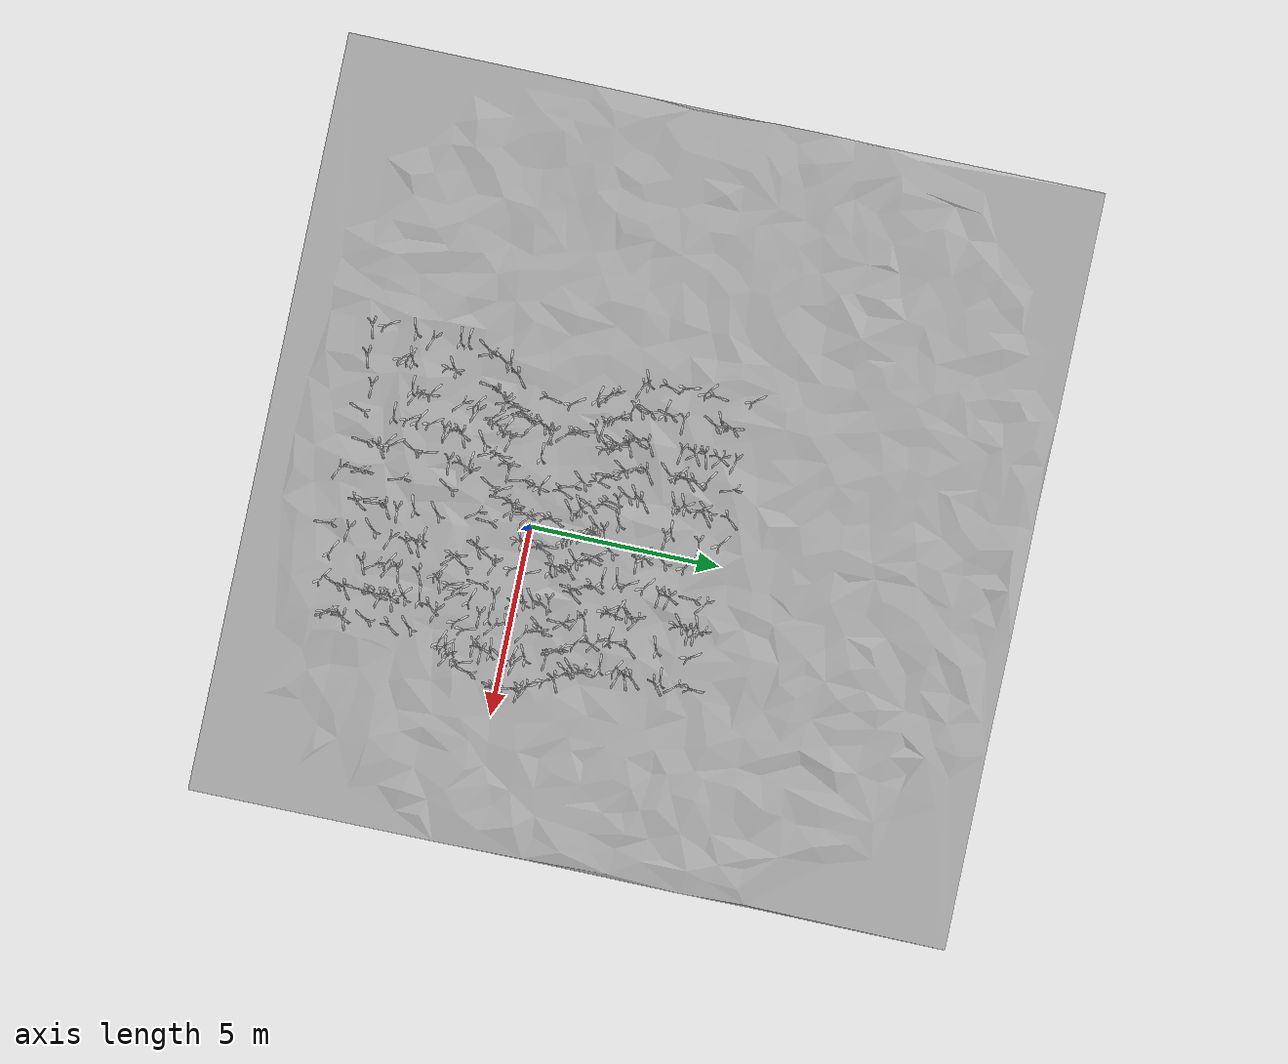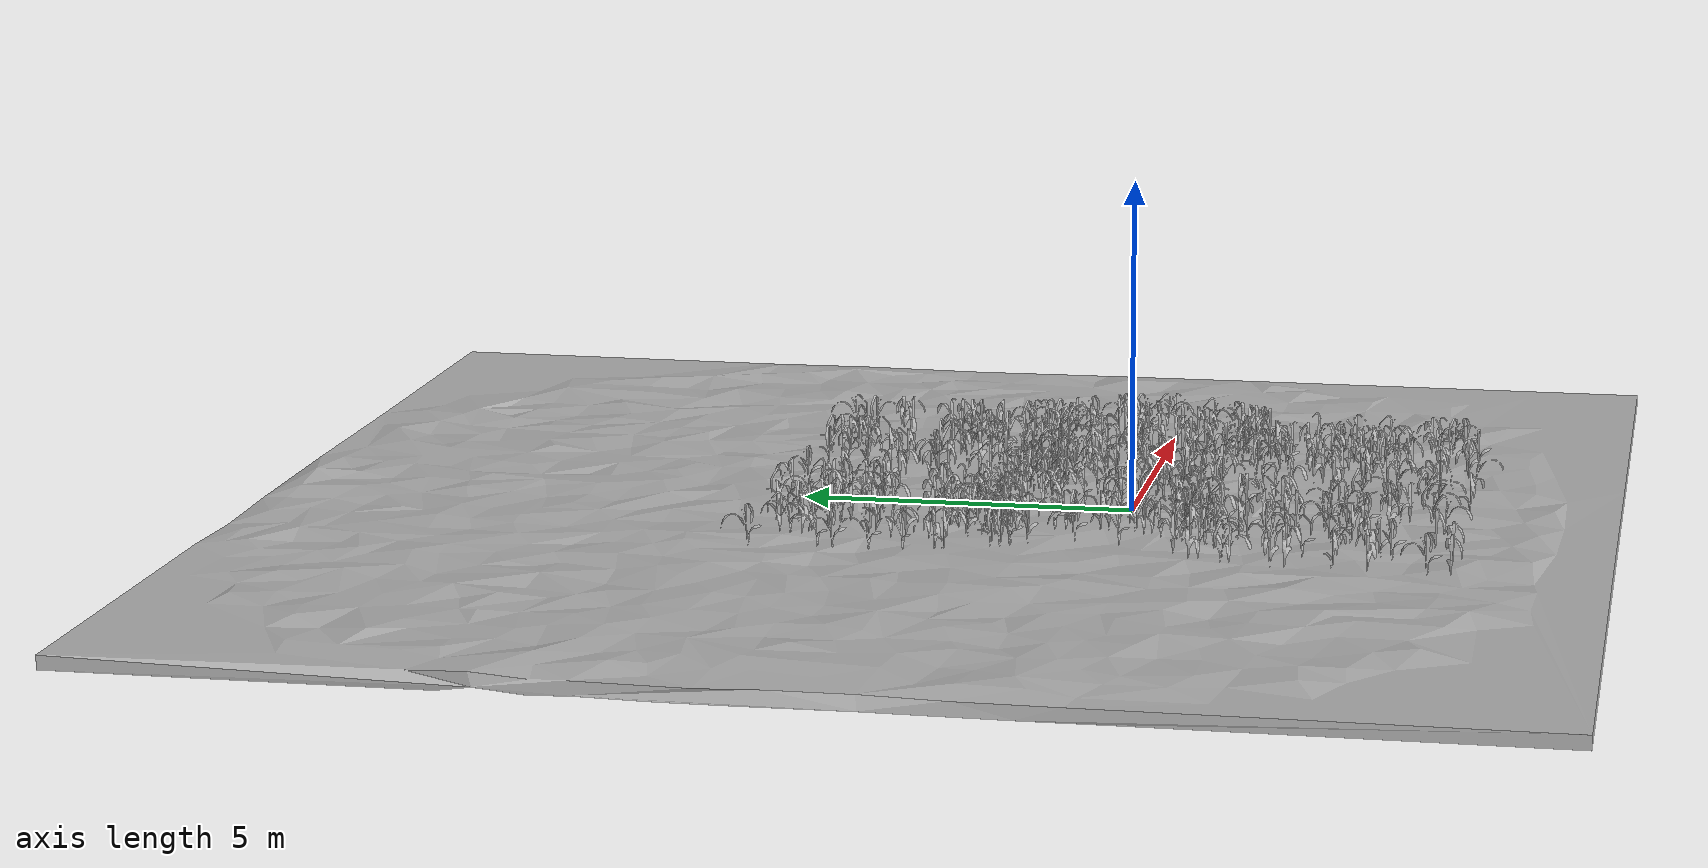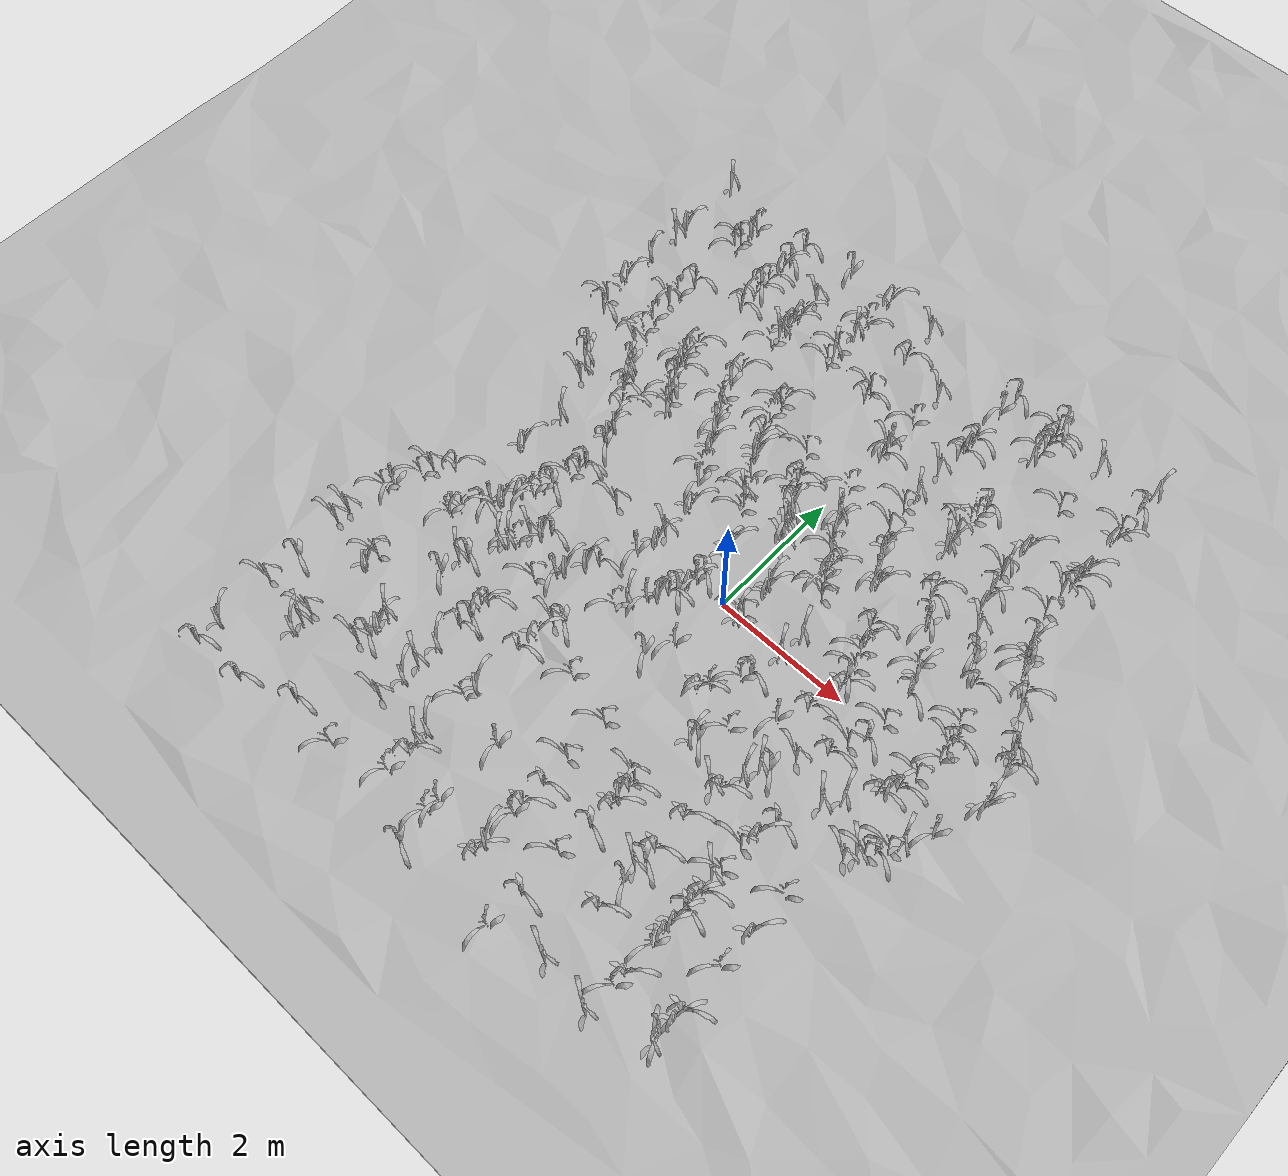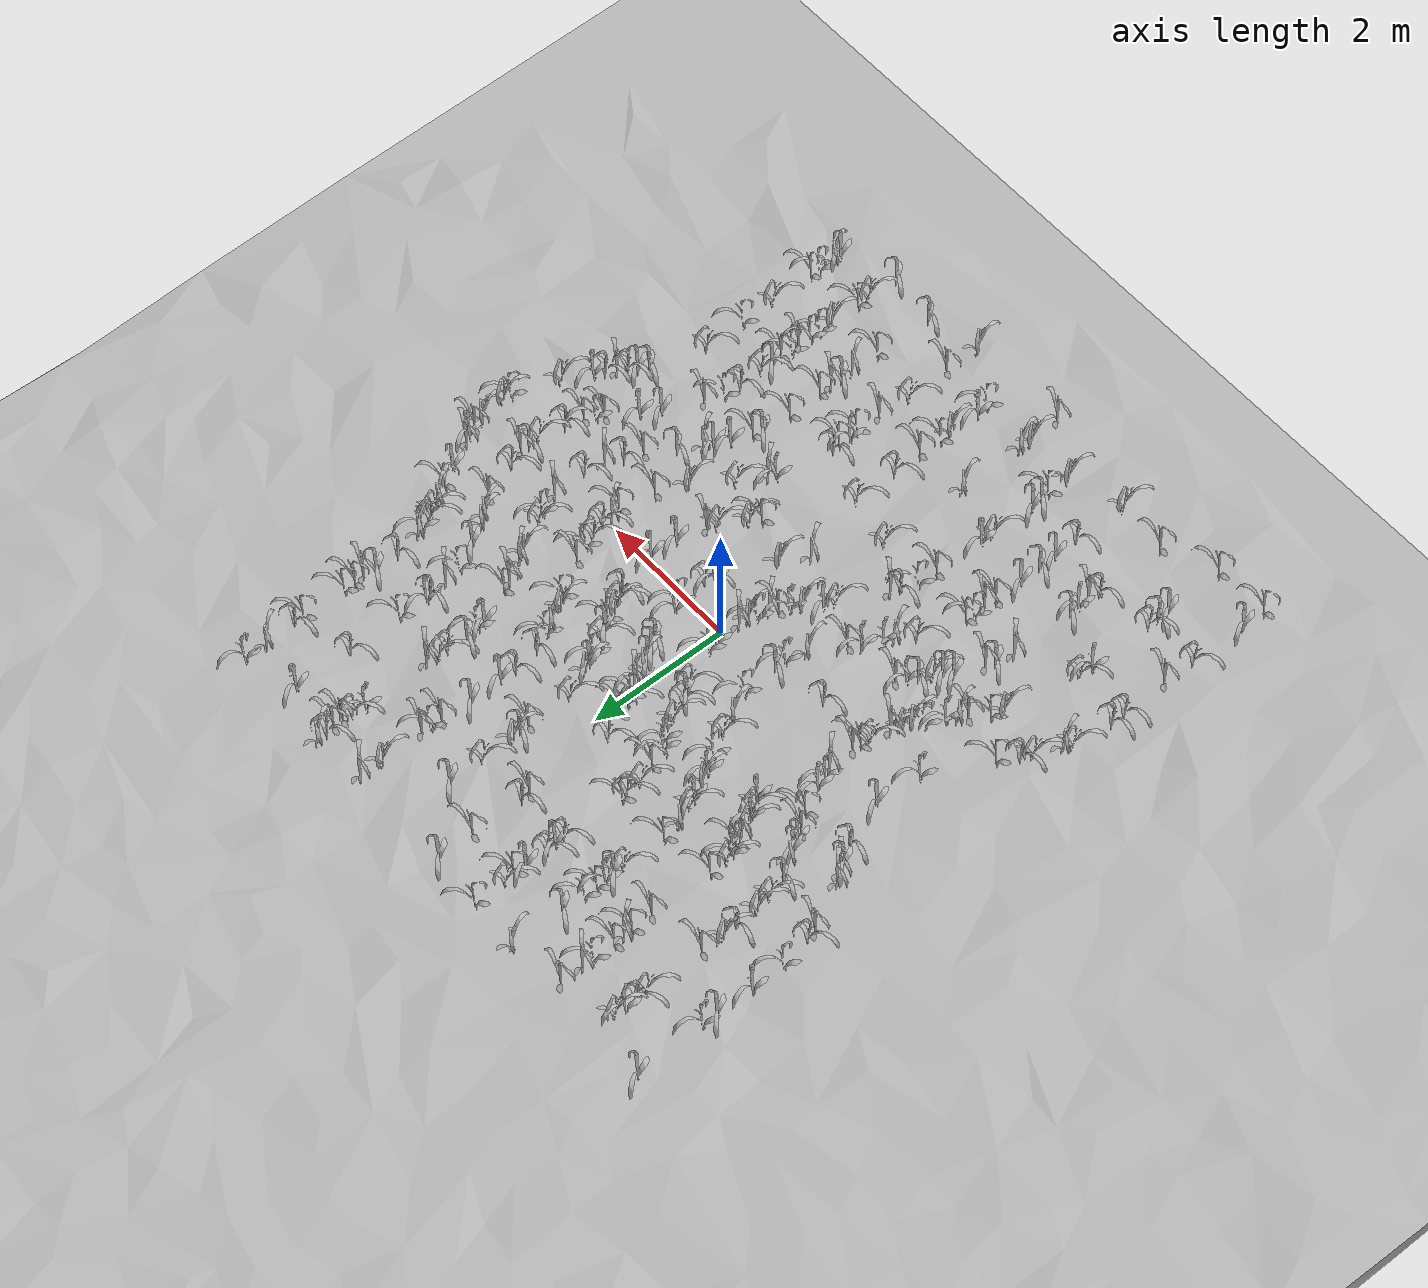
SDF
<sdf version="1.6">
 <world name="default">
  <light name="sun" type="directional">
   <pose>0 0 10 0 -0 0</pose>
   <diffuse>0.8 0.8 0.8 1</diffuse>
   <specular>0.2 0.2 0.2 1</specular>
   <attenuation>
    <range>1000</range>
    <constant>0.9</constant>
    <linear>0.01</linear>
    <quadratic>0.001</quadratic>
   </attenuation>
   <direction>-0.5 0.1 -0.9</direction>
  </light>
  <gravity>0 0 -9.8</gravity>
  <magnetic_field>6e-06 2.3e-05 -4.2e-05</magnetic_field>
  <atmosphere type="adiabatic"/>
  <physics name="default_physics" default="0" type="ode">
   <max_step_size>0.005</max_step_size>
   <real_time_factor>1</real_time_factor>
   <real_time_update_rate>200</real_time_update_rate>
  </physics>
  <scene>
   <sky><clouds><speed>12</speed></clouds></sky>
   <ambient>0.4 0.4 0.4 1</ambient>
   <background>0.7 0.7 0.7 1</background>
   <grid>false</grid>
   <shadows>1</shadows>
  </scene>
  <audio><device>default</device></audio>
  <spherical_coordinates>
   <surface_model>EARTH_WGS84</surface_model>
   <latitude_deg>0</latitude_deg>
   <longitude_deg>0</longitude_deg>
   <elevation>0</elevation>
   <heading_deg>0</heading_deg>
  </spherical_coordinates>
  <model name="custom_terrain">
   <static>1</static>
   <link name="link">
    <collision name="collision">
     <geometry><mesh><uri>model://custom_terrain/meshes/terrain.stl</uri></mesh></geometry>
    </collision>
    <visual name="visual">
     <geometry><mesh><uri>model://custom_terrain/meshes/terrain.stl</uri></mesh></geometry>
     <material>
      <script>
       <uri>model://custom_terrain/materials/scripts</uri>
       <uri>model://custom_terrain/materials/textures</uri>
       <name>custom_terrain/terrain</name>
      </script>
     </material>
    </visual>
   </link>
   <pose>-1.53507 2.74629 0.25 0 -0 0</pose>
  </model>
  <include>
   <uri>model://maize_01</uri>
   <pose>-4.3106219414862945 -5.04937802084627 0.2977664786555406 0.0 0.0 1.009872327117621</pose>
   <name>maize_01_0000</name>
   <static>true</static>
  </include>
  <include>
   <uri>model://maize_01</uri>
   <pose>-4.2867137522594 -4.708246365392506 0.29765879354210056 0.0 0.0 2.915274614726531</pose>
   <name>maize_01_0001</name>
   <static>true</static>
  </include>
  <include>
   <uri>model://maize_01</uri>
   <pose>-4.281053319347041 -3.8794299368986604 0.2970719017235535 0.0 0.0 4.273451764508771</pose>
   <name>maize_01_0003</name>
   <static>true</static>
  </include>
  <include>
   <uri>model://maize_01</uri>
   <pose>-4.287310599381049 -3.4019237235535367 0.2964022149720307 0.0 0.0 0.4347104957143591</pose>
   <name>maize_01_0005</name>
   <static>true</static>
  </include>
  <include>
   <uri>model://maize_01</uri>
   <pose>-4.295796902444148 -2.724274799269665 0.2958788721587244 0.0 0.0 4.046131409551049</pose>
   <name>maize_01_0006</name>
   <static>true</static>
  </include>
  <include>
   <uri>model://maize_01</uri>
   <pose>-4.293580158908372 -2.5229802013675995 0.2958788721587244 0.0 0.0 3.8800439426469624</pose>
   <name>maize_01_0007</name>
   <static>true</static>
  </include>
  <include>
   <uri>model://maize_01</uri>
   <pose>-4.2254993554903475 -1.9437898647088712 0.2966477008774588 0.0 0.0 4.847441126227612</pose>
   <name>maize_01_0010</name>
   <static>true</static>
  </include>
  <include>
   <uri>model://maize_01</uri>
   <pose>-4.1835285038470404 -1.8333754207803714 0.2966477008774588 0.0 0.0 5.892835990893525</pose>
   <name>maize_01_0011</name>
   <static>true</static>
  </include>
  <include>
   <uri>model://maize_01</uri>
   <pose>-4.022818136607775 -1.4842302419656674 0.2966477008774588 0.0 0.0 4.910755848312326</pose>
   <name>maize_01_0014</name>
   <static>true</static>
  </include>
  <include>
   <uri>model://maize_01</uri>
   <pose>-3.9592921442482782 -1.338071324385545 0.2966477008774588 0.0 0.0 4.022156642924693</pose>
   <name>maize_01_0015</name>
   <static>true</static>
  </include>
  <include>
   <uri>model://maize_01</uri>
   <pose>-3.798289916580425 -1.111770347679953 0.2966477008774588 0.0 0.0 1.434338322950149</pose>
   <name>maize_01_0017</name>
   <static>true</static>
  </include>
  <include>
   <uri>model://maize_01</uri>
   <pose>-3.3695648389005837 -0.2723812203231477 0.2990067847836856 0.0 0.0 2.181242108040814</pose>
   <name>maize_01_0020</name>
   <static>true</static>
  </include>
  <include>
   <uri>model://maize_01</uri>
   <pose>-3.3132409855095895 0.3800700148087619 0.2981828816108464 0.0 0.0 2.954021962010038</pose>
   <name>maize_01_0022</name>
   <static>true</static>
  </include>
  <include>
   <uri>model://maize_01</uri>
   <pose>-3.553511355616913 1.015519715591729 0.298130027727126 0.0 0.0 3.7159141833830094</pose>
   <name>maize_01_0024</name>
   <static>true</static>
  </include>
  <include>
   <uri>model://maize_01</uri>
   <pose>-3.701589226799579 1.251108949173141 0.298130027727126 0.0 0.0 3.122461391727913</pose>
   <name>maize_01_0026</name>
   <static>true</static>
  </include>
  <include>
   <uri>model://maize_01</uri>
   <pose>-3.785204417043643 1.3649316195686685 0.298130027727126 0.0 0.0 0.08165920619168597</pose>
   <name>maize_01_0027</name>
   <static>true</static>
  </include>
  <include>
   <uri>model://maize_01</uri>
   <pose>-3.8622362099861243 1.484537688607343 0.298130027727126 0.0 0.0 0.017328552184580254</pose>
   <name>maize_01_0028</name>
   <static>true</static>
  </include>
  <include>
   <uri>model://maize_01</uri>
   <pose>-4.197337103055846 2.1108192121852984 0.29843291746035566 0.0 0.0 0.45616426685301054</pose>
   <name>maize_01_0030</name>
   <static>true</static>
  </include>
  <include>
   <uri>model://maize_01</uri>
   <pose>-4.213425510401133 2.245129814301681 0.29843291746035566 0.0 0.0 4.282105960557281</pose>
   <name>maize_01_0031</name>
   <static>true</static>
  </include>
  <include>
   <uri>model://maize_01</uri>
   <pose>-4.303971360781282 2.6837327133476054 0.29843291746035566 0.0 0.0 2.0121442333241513</pose>
   <name>maize_01_0035</name>
   <static>true</static>
  </include>
  <include>
   <uri>model://maize_01</uri>
   <pose>-4.316781519382808 3.174394487851791 0.29843291746035566 0.0 0.0 2.603425036955321</pose>
   <name>maize_01_0038</name>
   <static>true</static>
  </include>
  <include>
   <uri>model://maize_01</uri>
   <pose>-4.285277259324883 3.702888524991318 0.30062281465596047 0.0 0.0 3.2110787540230965</pose>
   <name>maize_01_0040</name>
   <static>true</static>
  </include>
  <include>
   <uri>model://maize_01</uri>
   <pose>-4.292784419722234 3.919240395021373 0.30062281465596047 0.0 0.0 2.223316650808182</pose>
   <name>maize_01_0041</name>
   <static>true</static>
  </include>
  <include>
   <uri>model://maize_01</uri>
   <pose>-4.317581517556513 4.924926001546315 0.3005668615041675 0.0 0.0 3.024532714668203</pose>
   <name>maize_01_0043</name>
   <static>true</static>
  </include>
  <include>
   <uri>model://maize_01</uri>
   <pose>-3.538260925980875 -5.021662483610432 0.2967203590316047 0.0 0.0 1.0299678981490668</pose>
   <name>maize_01_0044</name>
   <static>true</static>
  </include>
  <include>
   <uri>model://maize_01</uri>
   <pose>-3.53552321622471 -4.162000822857167 0.29562531661520675 0.0 0.0 3.0065860364294803</pose>
   <name>maize_01_0045</name>
   <static>true</static>
  </include>
  <include>
   <uri>model://maize_01</uri>
   <pose>-3.531918482207313 -3.9933455633778006 0.29562531661520675 0.0 0.0 3.4749418017371942</pose>
   <name>maize_01_0046</name>
   <static>true</static>
  </include>
  <include>
   <uri>model://maize_01</uri>
   <pose>-3.542538107272777 -3.8281868389006863 0.29562531661520675 0.0 0.0 4.230603673084305</pose>
   <name>maize_01_0047</name>
   <static>true</static>
  </include>
  <include>
   <uri>model://maize_01</uri>
   <pose>-3.5526577792279395 -2.900068725105194 0.29562531661520675 0.0 0.0 2.441766853882377</pose>
   <name>maize_01_0053</name>
   <static>true</static>
  </include>
  <include>
   <uri>model://maize_01</uri>
   <pose>-3.5353557576555628 -2.6957962571806933 0.29562531661520675 0.0 0.0 4.463502437837743</pose>
   <name>maize_01_0054</name>
   <static>true</static>
  </include>
  <include>
   <uri>model://maize_01</uri>
   <pose>-3.335835348676938 -1.6375310743290308 0.29562531661520675 0.0 0.0 5.390432706229928</pose>
   <name>maize_01_0061</name>
   <static>true</static>
  </include>
  <include>
   <uri>model://maize_01</uri>
   <pose>-3.2811562548678688 -1.4942557103216776 0.29562531661520675 0.0 0.0 1.6037076923450477</pose>
   <name>maize_01_0062</name>
   <static>true</static>
  </include>
  <include>
   <uri>model://maize_01</uri>
   <pose>-3.123747730165093 -1.2653885932093727 0.29562531661520675 0.0 0.0 0.627559211468205</pose>
   <name>maize_01_0064</name>
   <static>true</static>
  </include>
  <include>
   <uri>model://maize_01</uri>
   <pose>-3.0515116640523985 -1.1473619694546942 0.29562531661520675 0.0 0.0 5.834372492273948</pose>
   <name>maize_01_0065</name>
   <static>true</static>
  </include>
  <include>
   <uri>model://maize_01</uri>
   <pose>-2.965289503134991 -1.0460428277923335 0.29562531661520675 0.0 0.0 2.258653648294244</pose>
   <name>maize_01_0066</name>
   <static>true</static>
  </include>
  <include>
   <uri>model://maize_01</uri>
   <pose>-2.8541772263172978 -0.8057247133422856 0.29562531661520675 0.0 0.0 1.9543898337898045</pose>
   <name>maize_01_0068</name>
   <static>true</static>
  </include>
  <include>
   <uri>model://maize_01</uri>
   <pose>-2.752196226297347 -0.6794381848965856 0.29562531661520675 0.0 0.0 5.5246225805519575</pose>
   <name>maize_01_0069</name>
   <static>true</static>
  </include>
  <include>
   <uri>model://maize_01</uri>
   <pose>-2.7126271128533053 -0.549616045358267 0.29562531661520675 0.0 0.0 5.256085428895383</pose>
   <name>maize_01_0070</name>
   <static>true</static>
  </include>
  <include>
   <uri>model://maize_01</uri>
   <pose>-2.6549400466816366 -0.42574120303755714 0.29562531661520675 0.0 0.0 0.25062780883100877</pose>
   <name>maize_01_0071</name>
   <static>true</static>
  </include>
  <include>
   <uri>model://maize_01</uri>
   <pose>-2.587292611984243 -0.15651339399301126 0.29562531661520675 0.0 0.0 4.6698939311208285</pose>
   <name>maize_01_0073</name>
   <static>true</static>
  </include>
  <include>
   <uri>model://maize_01</uri>
   <pose>-2.5738651612871104 -0.02563137744743063 0.29562531661520675 0.0 0.0 1.1048778762881901</pose>
   <name>maize_01_0074</name>
   <static>true</static>
  </include>
  <include>
   <uri>model://maize_01</uri>
   <pose>-2.569291240878448 0.10154498484975047 0.29562531661520675 0.0 0.0 0.5553903101164603</pose>
   <name>maize_01_0075</name>
   <static>true</static>
  </include>
  <include>
   <uri>model://maize_01</uri>
   <pose>-2.5873100536612568 0.49106919523139925 0.29562531661520675 0.0 0.0 6.280524038659252</pose>
   <name>maize_01_0078</name>
   <static>true</static>
  </include>
  <include>
   <uri>model://maize_01</uri>
   <pose>-2.6469571788114794 0.6029479741588053 0.29562531661520675 0.0 0.0 2.2692072327197814</pose>
   <name>maize_01_0079</name>
   <static>true</static>
  </include>
  <include>
   <uri>model://maize_01</uri>
   <pose>-2.6907755242412503 0.7586937102701199 0.29562531661520675 0.0 0.0 2.509799935226596</pose>
   <name>maize_01_0080</name>
   <static>true</static>
  </include>
  <include>
   <uri>model://maize_01</uri>
   <pose>-2.8762519124756376 1.1099151490145986 0.2974299765986175 0.0 0.0 1.2394152793384987</pose>
   <name>maize_01_0082</name>
   <static>true</static>
  </include>
  <include>
   <uri>model://maize_01</uri>
   <pose>-3.045825980551641 1.3301807007487356 0.2974299765986175 0.0 0.0 0.6792271526109787</pose>
   <name>maize_01_0084</name>
   <static>true</static>
  </include>
  <include>
   <uri>model://maize_01</uri>
   <pose>-3.1234285954471717 1.4644570050705015 0.2974299765986175 0.0 0.0 2.92769435021656</pose>
   <name>maize_01_0085</name>
   <static>true</static>
  </include>
  <include>
   <uri>model://maize_01</uri>
   <pose>-3.1669062256921063 1.5670221087370784 0.2974299765986175 0.0 0.0 2.89145526982978</pose>
   <name>maize_01_0086</name>
   <static>true</static>
  </include>
  <include>
   <uri>model://maize_01</uri>
   <pose>-3.2459566719002337 1.7065941584194124 0.2985292159367102 0.0 0.0 6.0024044824257485</pose>
   <name>maize_01_0087</name>
   <static>true</static>
  </include>
  <include>
   <uri>model://maize_01</uri>
   <pose>-3.3972870597738365 1.9240552792608507 0.2985292159367102 0.0 0.0 3.555198688931049</pose>
   <name>maize_01_0089</name>
   <static>true</static>
  </include>
  <include>
   <uri>model://maize_01</uri>
   <pose>-3.483455573924775 2.211342313481739 0.2983892592633433 0.0 0.0 4.8671116039445055</pose>
   <name>maize_01_0091</name>
   <static>true</static>
  </include>
  <include>
   <uri>model://maize_01</uri>
   <pose>-3.527028630317879 2.442533515859209 0.2983892592633433 0.0 0.0 5.169608127667474</pose>
   <name>maize_01_0093</name>
   <static>true</static>
  </include>
  <include>
   <uri>model://maize_01</uri>
   <pose>-3.5471102146072293 2.7803373220525445 0.2983892592633433 0.0 0.0 3.7348141024443686</pose>
   <name>maize_01_0096</name>
   <static>true</static>
  </include>
  <include>
   <uri>model://maize_01</uri>
   <pose>-3.5568660209007104 2.9892173744235895 0.2983892592633433 0.0 0.0 5.287605900317257</pose>
   <name>maize_01_0097</name>
   <static>true</static>
  </include>
  <include>
   <uri>model://maize_01</uri>
   <pose>-3.5463511296136407 3.297227253958344 0.2983892592633433 0.0 0.0 0.7904044780898526</pose>
   <name>maize_01_0099</name>
   <static>true</static>
  </include>
  <include>
   <uri>model://maize_01</uri>
   <pose>-3.5337960846812426 4.152628220210384 0.30055292686338814 0.0 0.0 4.967728544414715</pose>
   <name>maize_01_0101</name>
   <static>true</static>
  </include>
  <include>
   <uri>model://maize_01</uri>
   <pose>-3.5566000803272693 4.301455851341266 0.30055292686338814 0.0 0.0 4.3376047987825395</pose>
   <name>maize_01_0102</name>
   <static>true</static>
  </include>
  <include>
   <uri>model://maize_01</uri>
   <pose>-3.5581769839938397 4.471954401550181 0.30055292686338814 0.0 0.0 2.4865935297529904</pose>
   <name>maize_01_0103</name>
   <static>true</static>
  </include>
  <include>
   <uri>model://maize_01</uri>
   <pose>-3.5334510304083158 4.6262888151670145 0.30055292686338814 0.0 0.0 5.130359262817705</pose>
   <name>maize_01_0104</name>
   <static>true</static>
  </include>
  <include>
   <uri>model://maize_01</uri>
   <pose>-2.798964400070975 -4.728901577935113 0.2963914716773796 0.0 0.0 0.8106787566220299</pose>
   <name>maize_01_0109</name>
   <static>true</static>
  </include>
  <include>
   <uri>model://maize_01</uri>
   <pose>-2.805766632001518 -3.6899461198835484 0.2963914716773796 0.0 0.0 3.947043253267654</pose>
   <name>maize_01_0115</name>
   <static>true</static>
  </include>
  <include>
   <uri>model://maize_01</uri>
   <pose>-2.791025082744204 -3.531027675069019 0.2963914716773796 0.0 0.0 0.2955993628914184</pose>
   <name>maize_01_0116</name>
   <static>true</static>
  </include>
  <include>
   <uri>model://maize_01</uri>
   <pose>-2.783067807960729 -3.3784625274625792 0.2963914716773796 0.0 0.0 2.4498771285213046</pose>
   <name>maize_01_0117</name>
   <static>true</static>
  </include>
  <include>
   <uri>model://maize_01</uri>
   <pose>-2.789696186660033 -3.2200491160021687 0.2963914716773796 0.0 0.0 3.2973487120872504</pose>
   <name>maize_01_0118</name>
   <static>true</static>
  </include>
  <include>
   <uri>model://maize_01</uri>
   <pose>-2.8009565205610056 -2.297385516756142 0.2965412666649686 0.0 0.0 0.042924659762956556</pose>
   <name>maize_01_0121</name>
   <static>true</static>
  </include>
  <include>
   <uri>model://maize_01</uri>
   <pose>-2.738819103998608 -2.0394273470652684 0.2965412666649686 0.0 0.0 3.2857884913953685</pose>
   <name>maize_01_0123</name>
   <static>true</static>
  </include>
  <include>
   <uri>model://maize_01</uri>
   <pose>-2.708081434505685 -1.9094804849719786 0.2965412666649686 0.0 0.0 0.39676879773514157</pose>
   <name>maize_01_0124</name>
   <static>true</static>
  </include>
  <include>
   <uri>model://maize_01</uri>
   <pose>-2.5264795987889275 -1.5467656292137206 0.2965412666649686 0.0 0.0 3.0579781962675945</pose>
   <name>maize_01_0127</name>
   <static>true</static>
  </include>
  <include>
   <uri>model://maize_01</uri>
   <pose>-2.444564018720821 -1.4486002683070487 0.2965412666649686 0.0 0.0 3.043051343088415</pose>
   <name>maize_01_0128</name>
   <static>true</static>
  </include>
  <include>
   <uri>model://maize_01</uri>
   <pose>-2.393026826170004 -1.3219779207511053 0.2965412666649686 0.0 0.0 5.164440687180312</pose>
   <name>maize_01_0129</name>
   <static>true</static>
  </include>
  <include>
   <uri>model://maize_01</uri>
   <pose>-2.2985396233965787 -1.1717692314672912 0.2971929842640029 0.0 0.0 3.4702972293925427</pose>
   <name>maize_01_0130</name>
   <static>true</static>
  </include>
  <include>
   <uri>model://maize_01</uri>
   <pose>-2.2288614928046955 -1.0620732169063454 0.2971929842640029 0.0 0.0 2.4486771638649363</pose>
   <name>maize_01_0131</name>
   <static>true</static>
  </include>
  <include>
   <uri>model://maize_01</uri>
   <pose>-2.1642517371181826 -0.9409564305237252 0.2971929842640029 0.0 0.0 0.556910015923153</pose>
   <name>maize_01_0132</name>
   <static>true</static>
  </include>
  <include>
   <uri>model://maize_01</uri>
   <pose>-1.8060996930874265 -0.08265334749182543 0.2971929842640029 0.0 0.0 3.954166942049239</pose>
   <name>maize_01_0139</name>
   <static>true</static>
  </include>
  <include>
   <uri>model://maize_01</uri>
   <pose>-2.3542755942313485 1.4268677347338252 0.29802047241567764 0.0 0.0 2.671994580706277</pose>
   <name>maize_01_0149</name>
   <static>true</static>
  </include>
  <include>
   <uri>model://maize_01</uri>
   <pose>-2.419213127442763 1.5359117934384716 0.29802047241567764 0.0 0.0 4.736903949275797</pose>
   <name>maize_01_0150</name>
   <static>true</static>
  </include>
  <include>
   <uri>model://maize_01</uri>
   <pose>-2.50696249297475 1.656988620708584 0.29802047241567764 0.0 0.0 2.515227664649338</pose>
   <name>maize_01_0151</name>
   <static>true</static>
  </include>
  <include>
   <uri>model://maize_01</uri>
   <pose>-2.563210837394043 1.763402110522948 0.29802047241567764 0.0 0.0 5.0969894401205895</pose>
   <name>maize_01_0152</name>
   <static>true</static>
  </include>
  <include>
   <uri>model://maize_01</uri>
   <pose>-2.631932517354745 1.9154094356934717 0.29802047241567764 0.0 0.0 0.008795678634441244</pose>
   <name>maize_01_0153</name>
   <static>true</static>
  </include>
  <include>
   <uri>model://maize_01</uri>
   <pose>-2.670411633898165 2.0215566065165844 0.29802047241567764 0.0 0.0 1.1970025165682754</pose>
   <name>maize_01_0154</name>
   <static>true</static>
  </include>
  <include>
   <uri>model://maize_01</uri>
   <pose>-2.746698726054034 2.1493248034528434 0.29802047241567764 0.0 0.0 2.0213183076419163</pose>
   <name>maize_01_0155</name>
   <static>true</static>
  </include>
  <include>
   <uri>model://maize_01</uri>
   <pose>-2.7799440682236427 2.272083570431812 0.29802047241567764 0.0 0.0 5.0588659044747155</pose>
   <name>maize_01_0156</name>
   <static>true</static>
  </include>
  <include>
   <uri>model://maize_01</uri>
   <pose>-2.790767013238382 2.5212518864075446 0.29802047241567764 0.0 0.0 1.2863684499754549</pose>
   <name>maize_01_0158</name>
   <static>true</static>
  </include>
  <include>
   <uri>model://maize_01</uri>
   <pose>-2.7805146520129984 3.421578367413567 0.29802047241567764 0.0 0.0 0.6661819181573747</pose>
   <name>maize_01_0164</name>
   <static>true</static>
  </include>
  <include>
   <uri>model://maize_01</uri>
   <pose>-2.788451169182441 3.7259747708406175 0.29802047241567764 0.0 0.0 1.3353568345255835</pose>
   <name>maize_01_0166</name>
   <static>true</static>
  </include>
  <include>
   <uri>model://maize_01</uri>
   <pose>-2.799967677461566 3.8731282183029383 0.29802047241567764 0.0 0.0 6.206083872773956</pose>
   <name>maize_01_0167</name>
   <static>true</static>
  </include>
  <include>
   <uri>model://maize_01</uri>
   <pose>-2.806763757923239 4.008573551805932 0.29802047241567764 0.0 0.0 1.0605384510884583</pose>
   <name>maize_01_0168</name>
   <static>true</static>
  </include>
  <include>
   <uri>model://maize_01</uri>
   <pose>-2.798437820052176 4.320536305061766 0.29802047241567764 0.0 0.0 1.8719166095897908</pose>
   <name>maize_01_0170</name>
   <static>true</static>
  </include>
  <include>
   <uri>model://maize_01</uri>
   <pose>-2.801926679168956 4.499417458454736 0.29802047241567764 0.0 0.0 0.13820792651453787</pose>
   <name>maize_01_0171</name>
   <static>true</static>
  </include>
  <include>
   <uri>model://maize_01</uri>
   <pose>-2.813040589263109 4.833185391529553 0.29802047241567764 0.0 0.0 0.5423860228804193</pose>
   <name>maize_01_0173</name>
   <static>true</static>
  </include>
  <include>
   <uri>model://maize_01</uri>
   <pose>-2.037356937717711 -4.800465182478748 0.296079299522224 0.0 0.0 5.153472902711048</pose>
   <name>maize_01_0176</name>
   <static>true</static>
  </include>
  <include>
   <uri>model://maize_01</uri>
   <pose>-2.035642330818669 -4.008246143426293 0.296079299522224 0.0 0.0 3.983783290727368</pose>
   <name>maize_01_0180</name>
   <static>true</static>
  </include>
  <include>
   <uri>model://maize_01</uri>
   <pose>-2.0380250806052276 -3.6635137074793525 0.296079299522224 0.0 0.0 2.908492848086323</pose>
   <name>maize_01_0182</name>
   <static>true</static>
  </include>
  <include>
   <uri>model://maize_01</uri>
   <pose>-2.0371882653121873 -3.398683349203368 0.296079299522224 0.0 0.0 3.430149211889705</pose>
   <name>maize_01_0183</name>
   <static>true</static>
  </include>
  <include>
   <uri>model://maize_01</uri>
   <pose>-2.056095528594107 -3.0783429609287367 0.296079299522224 0.0 0.0 2.930114471328311</pose>
   <name>maize_01_0185</name>
   <static>true</static>
  </include>
  <include>
   <uri>model://maize_01</uri>
   <pose>-2.0677584263007325 -2.664400531791385 0.296079299522224 0.0 0.0 0.8231132626937595</pose>
   <name>maize_01_0187</name>
   <static>true</static>
  </include>
  <include>
   <uri>model://maize_01</uri>
   <pose>-2.0337813423427056 -2.50080096665875 0.296079299522224 0.0 0.0 0.3497517580661217</pose>
   <name>maize_01_0188</name>
   <static>true</static>
  </include>
  <include>
   <uri>model://maize_01</uri>
   <pose>-2.051436012982008 -2.328540965999518 0.296079299522224 0.0 0.0 1.8661755934966946</pose>
   <name>maize_01_0189</name>
   <static>true</static>
  </include>
  <include>
   <uri>model://maize_01</uri>
   <pose>-2.0385416068054436 -2.205119301068954 0.296079299522224 0.0 0.0 1.1257227018235436</pose>
   <name>maize_01_0190</name>
   <static>true</static>
  </include>
  <include>
   <uri>model://maize_01</uri>
   <pose>-1.83890950377934 -1.561768138190445 0.296079299522224 0.0 0.0 4.526946276829346</pose>
   <name>maize_01_0195</name>
   <static>true</static>
  </include>
  <include>
   <uri>model://maize_01</uri>
   <pose>-1.691355829389867 -1.325475131707669 0.29746583524542547 0.0 0.0 5.94947431856132</pose>
   <name>maize_01_0196</name>
   <static>true</static>
  </include>
  <include>
   <uri>model://maize_01</uri>
   <pose>-1.6347914479728687 -1.2267259251499538 0.29746583524542547 0.0 0.0 2.3978092316435413</pose>
   <name>maize_01_0197</name>
   <static>true</static>
  </include>
  <include>
   <uri>model://maize_01</uri>
   <pose>-1.4981555946733949 -0.9815268897275609 0.2978907654364121 0.0 0.0 2.346884400702729</pose>
   <name>maize_01_0198</name>
   <static>true</static>
  </include>
  <include>
   <uri>model://maize_01</uri>
   <pose>-1.4064770792423416 -0.8358375654999739 0.2978907654364121 0.0 0.0 0.7886028978380181</pose>
   <name>maize_01_0199</name>
   <static>true</static>
  </include>
  <include>
   <uri>model://maize_01</uri>
   <pose>-1.1592263770593656 -0.37667630154750165 0.29770103943925713 0.0 0.0 5.73840271277332</pose>
   <name>maize_01_0202</name>
   <static>true</static>
  </include>
  <include>
   <uri>model://maize_01</uri>
   <pose>-1.0766465211874803 -0.11838151379769382 0.29770103943925713 0.0 0.0 2.15506361575753</pose>
   <name>maize_01_0204</name>
   <static>true</static>
  </include>
  <include>
   <uri>model://maize_01</uri>
   <pose>-1.0471731540748108 0.03267209809383129 0.29770103943925713 0.0 0.0 3.438296545017204</pose>
   <name>maize_01_0205</name>
   <static>true</static>
  </include>
  <include>
   <uri>model://maize_01</uri>
   <pose>-1.106056116706976 0.5522489203266578 0.29853187421893257 0.0 0.0 1.9465953062249834</pose>
   <name>maize_01_0208</name>
   <static>true</static>
  </include>
  <include>
   <uri>model://maize_01</uri>
   <pose>-1.2744823994863455 0.9090987528574599 0.2983133183180139 0.0 0.0 5.747931553735355</pose>
   <name>maize_01_0210</name>
   <static>true</static>
  </include>
  <include>
   <uri>model://maize_01</uri>
   <pose>-1.3848780395915126 1.1412759801417038 0.2983133183180139 0.0 0.0 4.766547807838341</pose>
   <name>maize_01_0212</name>
   <static>true</static>
  </include>
  <include>
   <uri>model://maize_01</uri>
   <pose>-1.5379192895491889 1.4099271695368996 0.2983133183180139 0.0 0.0 2.08322205187894</pose>
   <name>maize_01_0214</name>
   <static>true</static>
  </include>
  <include>
   <uri>model://maize_01</uri>
   <pose>-1.6743975817590935 1.626297769316415 0.29858168232272014 0.0 0.0 2.4755370905607923</pose>
   <name>maize_01_0215</name>
   <static>true</static>
  </include>
  <include>
   <uri>model://maize_01</uri>
   <pose>-1.7452319155154934 1.7759325013317564 0.29858168232272014 0.0 0.0 5.582362585549439</pose>
   <name>maize_01_0216</name>
   <static>true</static>
  </include>
  <include>
   <uri>model://maize_01</uri>
   <pose>-1.8746929930001375 2.002556748294244 0.29858168232272014 0.0 0.0 2.8437651616951274</pose>
   <name>maize_01_0218</name>
   <static>true</static>
  </include>
  <include>
   <uri>model://maize_01</uri>
   <pose>-1.9203383463824324 2.115227414114837 0.29858168232272014 0.0 0.0 4.907377513593954</pose>
   <name>maize_01_0219</name>
   <static>true</static>
  </include>
  <include>
   <uri>model://maize_01</uri>
   <pose>-2.0219309184050633 2.375357779116198 0.29858168232272014 0.0 0.0 5.844364559026823</pose>
   <name>maize_01_0221</name>
   <static>true</static>
  </include>
  <include>
   <uri>model://maize_01</uri>
   <pose>-2.062503407745961 2.6249705897673956 0.29858168232272014 0.0 0.0 1.3853284582280792</pose>
   <name>maize_01_0224</name>
   <static>true</static>
  </include>
  <include>
   <uri>model://maize_01</uri>
   <pose>-2.053499766258849 3.256375381195037 0.29858168232272014 0.0 0.0 4.746885177144807</pose>
   <name>maize_01_0227</name>
   <static>true</static>
  </include>
  <include>
   <uri>model://maize_01</uri>
   <pose>-2.046209839599853 3.402475040709034 0.29858168232272014 0.0 0.0 3.2324683231455444</pose>
   <name>maize_01_0228</name>
   <static>true</static>
  </include>
  <include>
   <uri>model://maize_01</uri>
   <pose>-2.0582844487145926 3.533080885776514 0.29858168232272014 0.0 0.0 2.3312846641927583</pose>
   <name>maize_01_0229</name>
   <static>true</static>
  </include>
  <include>
   <uri>model://maize_01</uri>
   <pose>-2.066300592764047 3.664519510433174 0.29858168232272014 0.0 0.0 1.5580692882425378</pose>
   <name>maize_01_0230</name>
   <static>true</static>
  </include>
  <include>
   <uri>model://maize_01</uri>
   <pose>-2.065946663502853 3.8539702701908376 0.29858168232272014 0.0 0.0 1.7915803567850899</pose>
   <name>maize_01_0231</name>
   <static>true</static>
  </include>
  <include>
   <uri>model://maize_01</uri>
   <pose>-2.047825171950663 4.188539844633218 0.29858168232272014 0.0 0.0 3.3819264090446155</pose>
   <name>maize_01_0233</name>
   <static>true</static>
  </include>
  <include>
   <uri>model://maize_01</uri>
   <pose>-2.0460154160670636 4.967455718463136 0.29858168232272014 0.0 0.0 5.838906355624722</pose>
   <name>maize_01_0238</name>
   <static>true</static>
  </include>
  <include>
   <uri>model://maize_01</uri>
   <pose>-1.2804085820157127 -4.563180656179525 0.29590235500207257 0.0 0.0 5.395241899362856</pose>
   <name>maize_01_0242</name>
   <static>true</static>
  </include>
  <include>
   <uri>model://maize_01</uri>
   <pose>-1.2800712500359779 -4.251862335189655 0.29590235500207257 0.0 0.0 1.394198264005985</pose>
   <name>maize_01_0244</name>
   <static>true</static>
  </include>
  <include>
   <uri>model://maize_01</uri>
   <pose>-1.2950705056804146 -4.097692553778722 0.29590235500207257 0.0 0.0 3.281134934650724</pose>
   <name>maize_01_0245</name>
   <static>true</static>
  </include>
  <include>
   <uri>model://maize_01</uri>
   <pose>-1.313031535116563 -3.9415124170670404 0.29590235500207257 0.0 0.0 3.0001504648503694</pose>
   <name>maize_01_0246</name>
   <static>true</static>
  </include>
  <include>
   <uri>model://maize_01</uri>
   <pose>-1.3069329628613324 -3.2821441129302413 0.29590235500207257 0.0 0.0 5.015694495883181</pose>
   <name>maize_01_0250</name>
   <static>true</static>
  </include>
  <include>
   <uri>model://maize_01</uri>
   <pose>-1.2992617623044185 -3.116479382136433 0.29590235500207257 0.0 0.0 2.6340493697281713</pose>
   <name>maize_01_0251</name>
   <static>true</static>
  </include>
  <include>
   <uri>model://maize_01</uri>
   <pose>-1.293063249368452 -2.3883614056016236 0.2980741951089132 0.0 0.0 0.8616638235717357</pose>
   <name>maize_01_0255</name>
   <static>true</static>
  </include>
  <include>
   <uri>model://maize_01</uri>
   <pose>-1.2624484936386728 -2.1166297274187373 0.2980741951089132 0.0 0.0 1.8905516127639015</pose>
   <name>maize_01_0257</name>
   <static>true</static>
  </include>
  <include>
   <uri>model://maize_01</uri>
   <pose>-1.192283691249736 -1.856875570603352 0.2980741951089132 0.0 0.0 3.788098320756451</pose>
   <name>maize_01_0259</name>
   <static>true</static>
  </include>
  <include>
   <uri>model://maize_01</uri>
   <pose>-1.1460127619319997 -1.748088106887496 0.2980741951089132 0.0 0.0 0.15669133421016462</pose>
   <name>maize_01_0260</name>
   <static>true</static>
  </include>
  <include>
   <uri>model://maize_01</uri>
   <pose>-0.8208656052007306 -1.1326420935343118 0.2980741951089132 0.0 0.0 5.014500958465196</pose>
   <name>maize_01_0265</name>
   <static>true</static>
  </include>
  <include>
   <uri>model://maize_01</uri>
   <pose>-0.7468527770501685 -1.0127676385242685 0.2980741951089132 0.0 0.0 2.8490915135014325</pose>
   <name>maize_01_0266</name>
   <static>true</static>
  </include>
  <include>
   <uri>model://maize_01</uri>
   <pose>-0.6025579601264182 -0.7824202194122754 0.2980741951089132 0.0 0.0 5.545254523225686</pose>
   <name>maize_01_0268</name>
   <static>true</static>
  </include>
  <include>
   <uri>model://maize_01</uri>
   <pose>-0.5237663778298705 -0.6640728696754954 0.2980741951089132 0.0 0.0 2.256435803264442</pose>
   <name>maize_01_0269</name>
   <static>true</static>
  </include>
  <include>
   <uri>model://maize_01</uri>
   <pose>-0.4694573827493398 -0.5386795549778667 0.2980741951089132 0.0 0.0 0.8441177207310584</pose>
   <name>maize_01_0270</name>
   <static>true</static>
  </include>
  <include>
   <uri>model://maize_01</uri>
   <pose>-0.409251279057661 -0.43103615786844807 0.2980741951089132 0.0 0.0 6.26250552645099</pose>
   <name>maize_01_0271</name>
   <static>true</static>
  </include>
  <include>
   <uri>model://maize_01</uri>
   <pose>-0.3548659757521839 -0.28609927003604096 0.2980741951089132 0.0 0.0 1.9971027871010152</pose>
   <name>maize_01_0272</name>
   <static>true</static>
  </include>
  <include>
   <uri>model://maize_01</uri>
   <pose>-0.31297148360722304 -0.1626308074066201 0.2980741951089132 0.0 0.0 5.60605486878545</pose>
   <name>maize_01_0273</name>
   <static>true</static>
  </include>
  <include>
   <uri>model://maize_01</uri>
   <pose>-0.3161077779980579 -0.024136344394928316 0.2980741951089132 0.0 0.0 0.11755177830041272</pose>
   <name>maize_01_0274</name>
   <static>true</static>
  </include>
  <include>
   <uri>model://maize_01</uri>
   <pose>-0.32970329074596916 0.3419904858873879 0.2980741951089132 0.0 0.0 2.393773555222082</pose>
   <name>maize_01_0277</name>
   <static>true</static>
  </include>
  <include>
   <uri>model://maize_01</uri>
   <pose>-0.34477508339463436 0.4737825990442619 0.2980741951089132 0.0 0.0 1.9555725965990622</pose>
   <name>maize_01_0278</name>
   <static>true</static>
  </include>
  <include>
   <uri>model://maize_01</uri>
   <pose>-0.5801494302176928 0.9905428644980832 0.2980741951089132 0.0 0.0 4.595953194583849</pose>
   <name>maize_01_0282</name>
   <static>true</static>
  </include>
  <include>
   <uri>model://maize_01</uri>
   <pose>-0.6543607989581164 1.1173805844661489 0.2980741951089132 0.0 0.0 3.2355891034607653</pose>
   <name>maize_01_0283</name>
   <static>true</static>
  </include>
  <include>
   <uri>model://maize_01</uri>
   <pose>-0.7174633667288968 1.212257223490443 0.2980741951089132 0.0 0.0 4.450079179958104</pose>
   <name>maize_01_0284</name>
   <static>true</static>
  </include>
  <include>
   <uri>model://maize_01</uri>
   <pose>-0.8469761066933892 1.4764011923994855 0.2980741951089132 0.0 0.0 5.109657346527614</pose>
   <name>maize_01_0286</name>
   <static>true</static>
  </include>
  <include>
   <uri>model://maize_01</uri>
   <pose>-0.9889649496227195 1.7141858316516954 0.2980741951089132 0.0 0.0 2.1536230761633113</pose>
   <name>maize_01_0288</name>
   <static>true</static>
  </include>
  <include>
   <uri>model://maize_01</uri>
   <pose>-1.0839801235890352 1.8146651935052451 0.2980741951089132 0.0 0.0 2.1647313836325526</pose>
   <name>maize_01_0289</name>
   <static>true</static>
  </include>
  <include>
   <uri>model://maize_01</uri>
   <pose>-1.1895305549443937 2.077654672223105 0.2980741951089132 0.0 0.0 0.9991064376479477</pose>
   <name>maize_01_0291</name>
   <static>true</static>
  </include>
  <include>
   <uri>model://maize_01</uri>
   <pose>-1.2704914737936546 2.3454684826917984 0.2980741951089132 0.0 0.0 4.912695766120722</pose>
   <name>maize_01_0293</name>
   <static>true</static>
  </include>
  <include>
   <uri>model://maize_01</uri>
   <pose>-1.2860187935230625 2.5747495622239414 0.2980741951089132 0.0 0.0 4.5241118627285735</pose>
   <name>maize_01_0295</name>
   <static>true</static>
  </include>
  <include>
   <uri>model://maize_01</uri>
   <pose>-1.3142195178559228 2.6494565233816725 0.2980741951089132 0.0 0.0 1.4324338881868077</pose>
   <name>maize_01_0296</name>
   <static>true</static>
  </include>
  <include>
   <uri>model://maize_01</uri>
   <pose>-1.280420539230551 3.5389030344023724 0.2980741951089132 0.0 0.0 4.325825151307318</pose>
   <name>maize_01_0301</name>
   <static>true</static>
  </include>
  <include>
   <uri>model://maize_01</uri>
   <pose>-1.2880828729918445 3.663879295782172 0.2980741951089132 0.0 0.0 2.9036517979848706</pose>
   <name>maize_01_0302</name>
   <static>true</static>
  </include>
  <include>
   <uri>model://maize_01</uri>
   <pose>-1.3016144705972545 3.8060998656120053 0.2980741951089132 0.0 0.0 4.354085990940933</pose>
   <name>maize_01_0303</name>
   <static>true</static>
  </include>
  <include>
   <uri>model://maize_01</uri>
   <pose>-1.2918106301627315 4.1205459200696 0.2980741951089132 0.0 0.0 2.926563206481489</pose>
   <name>maize_01_0305</name>
   <static>true</static>
  </include>
  <include>
   <uri>model://maize_01</uri>
   <pose>-1.281527545851622 4.28620809062276 0.2980741951089132 0.0 0.0 1.4436792329718686</pose>
   <name>maize_01_0306</name>
   <static>true</static>
  </include>
  <include>
   <uri>model://maize_01</uri>
   <pose>-1.313386455114203 4.4564165047531885 0.2980741951089132 0.0 0.0 4.839911442866686</pose>
   <name>maize_01_0307</name>
   <static>true</static>
  </include>
  <include>
   <uri>model://maize_01</uri>
   <pose>-1.315002893785007 4.908616776108329 0.2980741951089132 0.0 0.0 1.6432664125197873</pose>
   <name>maize_01_0310</name>
   <static>true</static>
  </include>
  <include>
   <uri>model://maize_01</uri>
   <pose>-0.5384754639912608 -5.067289516835003 0.29734802537012744 0.0 0.0 0.3723138998509496</pose>
   <name>maize_01_0311</name>
   <static>true</static>
  </include>
  <include>
   <uri>model://maize_01</uri>
   <pose>-0.5645355800366321 -4.5885972361233005 0.29734802537012744 0.0 0.0 5.457467963302976</pose>
   <name>maize_01_0314</name>
   <static>true</static>
  </include>
  <include>
   <uri>model://maize_01</uri>
   <pose>-0.5525529923941492 -4.41396864098193 0.29734802537012744 0.0 0.0 5.772218835325074</pose>
   <name>maize_01_0315</name>
   <static>true</static>
  </include>
  <include>
   <uri>model://maize_01</uri>
   <pose>-0.5587905202653378 -3.445118525574791 0.2977097757156513 0.0 0.0 5.808318584392036</pose>
   <name>maize_01_0317</name>
   <static>true</static>
  </include>
  <include>
   <uri>model://maize_01</uri>
   <pose>-0.5285118431467952 -2.18277415802182 0.29888404200129726 0.0 0.0 4.931560564659485</pose>
   <name>maize_01_0320</name>
   <static>true</static>
  </include>
  <include>
   <uri>model://maize_01</uri>
   <pose>-0.11939909712865873 -1.3505968449950967 0.2984862012051281 0.0 0.0 6.109296820795949</pose>
   <name>maize_01_0323</name>
   <static>true</static>
  </include>
  <include>
   <uri>model://maize_01</uri>
   <pose>0.0837472966247936 -0.995230409187805 0.29829720678579147 0.0 0.0 5.442704468630226</pose>
   <name>maize_01_0324</name>
   <static>true</static>
  </include>
  <include>
   <uri>model://maize_01</uri>
   <pose>0.4017657940431254 -0.24631865214441298 0.29880351785391385 0.0 0.0 2.565142958011602</pose>
   <name>maize_01_0326</name>
   <static>true</static>
  </include>
  <include>
   <uri>model://maize_01</uri>
   <pose>0.4536182626695664 -0.12099326328731255 0.29880351785391385 0.0 0.0 4.321628640378749</pose>
   <name>maize_01_0327</name>
   <static>true</static>
  </include>
  <include>
   <uri>model://maize_01</uri>
   <pose>0.43379128000141143 0.29924030317328554 0.29880351785391385 0.0 0.0 2.008618362597867</pose>
   <name>maize_01_0330</name>
   <static>true</static>
  </include>
  <include>
   <uri>model://maize_01</uri>
   <pose>0.3802948406248967 0.4060382863086536 0.29880351785391385 0.0 0.0 2.3868585341959467</pose>
   <name>maize_01_0331</name>
   <static>true</static>
  </include>
  <include>
   <uri>model://maize_01</uri>
   <pose>0.18383181959480918 0.8958662362796985 0.2989652620931421 0.0 0.0 3.467905282745081</pose>
   <name>maize_01_0332</name>
   <static>true</static>
  </include>
  <include>
   <uri>model://maize_01</uri>
   <pose>0.10682219940322188 1.0131280186698228 0.2989652620931421 0.0 0.0 3.183100526046274</pose>
   <name>maize_01_0333</name>
   <static>true</static>
  </include>
  <include>
   <uri>model://maize_01</uri>
   <pose>0.03365599726035004 1.1314495480487918 0.2989652620931421 0.0 0.0 3.1187245882606707</pose>
   <name>maize_01_0334</name>
   <static>true</static>
  </include>
  <include>
   <uri>model://maize_01</uri>
   <pose>-0.030139900420178806 1.2696227397076558 0.2989652620931421 0.0 0.0 5.77605681294345</pose>
   <name>maize_01_0335</name>
   <static>true</static>
  </include>
  <include>
   <uri>model://maize_01</uri>
   <pose>-0.11407215265357198 1.4069969621074498 0.2989652620931421 0.0 0.0 2.4476001732700423</pose>
   <name>maize_01_0336</name>
   <static>true</static>
  </include>
  <include>
   <uri>model://maize_01</uri>
   <pose>-0.16986459446601312 1.516236006624349 0.2989652620931421 0.0 0.0 0.1114111442825732</pose>
   <name>maize_01_0337</name>
   <static>true</static>
  </include>
  <include>
   <uri>model://maize_01</uri>
   <pose>-0.247844698500318 1.6207478159505777 0.2989652620931421 0.0 0.0 1.531674634833781</pose>
   <name>maize_01_0338</name>
   <static>true</static>
  </include>
  <include>
   <uri>model://maize_01</uri>
   <pose>-0.33094973357394797 1.731561252301305 0.2989652620931421 0.0 0.0 4.771514243634816</pose>
   <name>maize_01_0339</name>
   <static>true</static>
  </include>
  <include>
   <uri>model://maize_01</uri>
   <pose>-0.37171589499352886 1.8765283585709527 0.2989652620931421 0.0 0.0 0.9279598226448749</pose>
   <name>maize_01_0340</name>
   <static>true</static>
  </include>
  <include>
   <uri>model://maize_01</uri>
   <pose>-0.5325088738870665 2.237318713420964 0.3002092080228909 0.0 0.0 4.338207076772166</pose>
   <name>maize_01_0341</name>
   <static>true</static>
  </include>
  <include>
   <uri>model://maize_01</uri>
   <pose>-0.5451103749846105 3.4491076114931123 0.2995136288696401 0.0 0.0 0.780050777093096</pose>
   <name>maize_01_0345</name>
   <static>true</static>
  </include>
  <include>
   <uri>model://maize_01</uri>
   <pose>-0.5416069639332453 3.5845922800494283 0.2995136288696401 0.0 0.0 4.036095894820048</pose>
   <name>maize_01_0346</name>
   <static>true</static>
  </include>
  <include>
   <uri>model://maize_01</uri>
   <pose>-0.5474769732693436 4.326999671468504 0.30031936771219947 0.0 0.0 0.8867513148687852</pose>
   <name>maize_01_0349</name>
   <static>true</static>
  </include>
  <include>
   <uri>model://maize_01</uri>
   <pose>-0.534264697549663 4.839853326514816 0.3001846581496553 0.0 0.0 3.2675767126063993</pose>
   <name>maize_01_0350</name>
   <static>true</static>
  </include>
  <include>
   <uri>model://maize_01</uri>
   <pose>0.20654496567249378 -4.563698720086001 0.2991276612406199 0.0 0.0 1.742323618467075</pose>
   <name>maize_01_0352</name>
   <static>true</static>
  </include>
  <include>
   <uri>model://maize_01</uri>
   <pose>0.18633684128090053 -4.389612200991711 0.2991276612406199 0.0 0.0 2.630046320601499</pose>
   <name>maize_01_0353</name>
   <static>true</static>
  </include>
  <include>
   <uri>model://maize_01</uri>
   <pose>0.20274988656522616 -3.915190070401967 0.2984457617101832 0.0 0.0 5.586733121383228</pose>
   <name>maize_01_0356</name>
   <static>true</static>
  </include>
  <include>
   <uri>model://maize_01</uri>
   <pose>0.18474293787067417 -3.7670939147733153 0.2984457617101832 0.0 0.0 1.2899176590988417</pose>
   <name>maize_01_0357</name>
   <static>true</static>
  </include>
  <include>
   <uri>model://maize_01</uri>
   <pose>0.19498251255593654 -3.4281366653964596 0.2982078223830002 0.0 0.0 0.8647332920321309</pose>
   <name>maize_01_0358</name>
   <static>true</static>
  </include>
  <include>
   <uri>model://maize_01</uri>
   <pose>0.1930449404539478 -2.995053472781806 0.2982078223830002 0.0 0.0 4.250910351826678</pose>
   <name>maize_01_0360</name>
   <static>true</static>
  </include>
  <include>
   <uri>model://maize_01</uri>
   <pose>0.18767564738893558 -2.3577712118431102 0.29887246608530155 0.0 0.0 4.599319493007212</pose>
   <name>maize_01_0361</name>
   <static>true</static>
  </include>
  <include>
   <uri>model://maize_01</uri>
   <pose>0.6918065554317978 -1.2648883115144731 0.29911194074011666 0.0 0.0 1.256339695371534</pose>
   <name>maize_01_0366</name>
   <static>true</static>
  </include>
  <include>
   <uri>model://maize_01</uri>
   <pose>0.7868503615200078 -1.120323634206185 0.29911194074011666 0.0 0.0 5.177257225411896</pose>
   <name>maize_01_0367</name>
   <static>true</static>
  </include>
  <include>
   <uri>model://maize_01</uri>
   <pose>0.9989920983704852 -0.7825476098136364 0.29911194074011666 0.0 0.0 5.00178853149674</pose>
   <name>maize_01_0370</name>
   <static>true</static>
  </include>
  <include>
   <uri>model://maize_01</uri>
   <pose>1.0391518489795029 -0.6588313700637232 0.29911194074011666 0.0 0.0 0.40643411764076687</pose>
   <name>maize_01_0371</name>
   <static>true</static>
  </include>
  <include>
   <uri>model://maize_01</uri>
   <pose>1.1562366235306916 -0.2669898493496332 0.29911194074011666 0.0 0.0 2.8488454676147277</pose>
   <name>maize_01_0373</name>
   <static>true</static>
  </include>
  <include>
   <uri>model://maize_01</uri>
   <pose>1.1878954285813224 0.11405326153645376 0.29963800878834257 0.0 0.0 2.76728954402455</pose>
   <name>maize_01_0374</name>
   <static>true</static>
  </include>
  <include>
   <uri>model://maize_01</uri>
   <pose>1.012828374834897 0.7353172180094185 0.2993062523895748 0.0 0.0 3.9300456820366896</pose>
   <name>maize_01_0376</name>
   <static>true</static>
  </include>
  <include>
   <uri>model://maize_01</uri>
   <pose>0.912483548576519 0.8740058016692058 0.2993062523895748 0.0 0.0 4.674985481229111</pose>
   <name>maize_01_0377</name>
   <static>true</static>
  </include>
  <include>
   <uri>model://maize_01</uri>
   <pose>0.8467944789519872 0.9890255482569976 0.2993062523895748 0.0 0.0 5.393729415344692</pose>
   <name>maize_01_0378</name>
   <static>true</static>
  </include>
  <include>
   <uri>model://maize_01</uri>
   <pose>0.7930646753303605 1.1227019811757557 0.2993062523895748 0.0 0.0 1.5592919034997363</pose>
   <name>maize_01_0379</name>
   <static>true</static>
  </include>
  <include>
   <uri>model://maize_01</uri>
   <pose>0.7101213813682363 1.2471427965538016 0.2993062523895748 0.0 0.0 3.1701744162668226</pose>
   <name>maize_01_0380</name>
   <static>true</static>
  </include>
  <include>
   <uri>model://maize_01</uri>
   <pose>0.6414324652614896 1.3657087246369624 0.2993062523895748 0.0 0.0 4.6450665034504475</pose>
   <name>maize_01_0381</name>
   <static>true</static>
  </include>
  <include>
   <uri>model://maize_01</uri>
   <pose>0.49301208837098787 1.5984581411932106 0.29894575445257004 0.0 0.0 2.1838838725683924</pose>
   <name>maize_01_0382</name>
   <static>true</static>
  </include>
  <include>
   <uri>model://maize_01</uri>
   <pose>0.4282886814252407 1.7213777871286966 0.29894575445257004 0.0 0.0 2.973416190661603</pose>
   <name>maize_01_0383</name>
   <static>true</static>
  </include>
  <include>
   <uri>model://maize_01</uri>
   <pose>0.3800023817713878 1.8423235570081855 0.29894575445257004 0.0 0.0 5.534383781625639</pose>
   <name>maize_01_0384</name>
   <static>true</static>
  </include>
  <include>
   <uri>model://maize_01</uri>
   <pose>0.2188367861700182 2.2133814139831434 0.29894575445257004 0.0 0.0 4.7784327291552495</pose>
   <name>maize_01_0387</name>
   <static>true</static>
  </include>
  <include>
   <uri>model://maize_01</uri>
   <pose>0.21326600575123653 2.8480899628144463 0.3005394333242308 0.0 0.0 0.8484978051286923</pose>
   <name>maize_01_0389</name>
   <static>true</static>
  </include>
  <include>
   <uri>model://maize_01</uri>
   <pose>0.2193484533585159 2.9879449052466858 0.3005394333242308 0.0 0.0 3.472309276198551</pose>
   <name>maize_01_0390</name>
   <static>true</static>
  </include>
  <include>
   <uri>model://maize_01</uri>
   <pose>0.18811778829982437 3.122969712779034 0.3005394333242308 0.0 0.0 5.433367640292908</pose>
   <name>maize_01_0391</name>
   <static>true</static>
  </include>
  <include>
   <uri>model://maize_01</uri>
   <pose>0.19607369249313208 3.584910728009977 0.2990346057010371 0.0 0.0 4.801097184111575</pose>
   <name>maize_01_0392</name>
   <static>true</static>
  </include>
  <include>
   <uri>model://maize_01</uri>
   <pose>0.20859107375786554 4.078234861976232 0.29922777058073424 0.0 0.0 3.2755222667623034</pose>
   <name>maize_01_0393</name>
   <static>true</static>
  </include>
  <include>
   <uri>model://maize_01</uri>
   <pose>0.9472404348529746 -5.051776723698589 0.2997558965364322 0.0 0.0 5.571469050402177</pose>
   <name>maize_01_0396</name>
   <static>true</static>
  </include>
  <include>
   <uri>model://maize_01</uri>
   <pose>0.9349636103348054 -4.532362831063865 0.2992296127409701 0.0 0.0 0.6429925623250854</pose>
   <name>maize_01_0399</name>
   <static>true</static>
  </include>
  <include>
   <uri>model://maize_01</uri>
   <pose>0.9323754764906578 -3.8867810460009182 0.2992296127409701 0.0 0.0 4.705035771135606</pose>
   <name>maize_01_0403</name>
   <static>true</static>
  </include>
  <include>
   <uri>model://maize_01</uri>
   <pose>0.9515196137624267 -3.4099812057607486 0.2990923173278823 0.0 0.0 0.40677968785936813</pose>
   <name>maize_01_0406</name>
   <static>true</static>
  </include>
  <include>
   <uri>model://maize_01</uri>
   <pose>0.9647895714538455 -3.059773605368395 0.2990923173278823 0.0 0.0 1.4293387663289825</pose>
   <name>maize_01_0408</name>
   <static>true</static>
  </include>
  <include>
   <uri>model://maize_01</uri>
   <pose>0.9392173863405222 -2.9224565859595146 0.2990923173278823 0.0 0.0 2.4449182117018204</pose>
   <name>maize_01_0409</name>
   <static>true</static>
  </include>
  <include>
   <uri>model://maize_01</uri>
   <pose>0.9637142258749545 -2.7656637203737695 0.2990923173278823 0.0 0.0 1.1147511036166706</pose>
   <name>maize_01_0410</name>
   <static>true</static>
  </include>
  <include>
   <uri>model://maize_01</uri>
   <pose>0.9352607802233928 -2.6223949783651435 0.2990923173278823 0.0 0.0 3.880504734463562</pose>
   <name>maize_01_0411</name>
   <static>true</static>
  </include>
  <include>
   <uri>model://maize_01</uri>
   <pose>1.087434395943119 -1.8351979483109513 0.2990923173278823 0.0 0.0 2.4553955416966526</pose>
   <name>maize_01_0417</name>
   <static>true</static>
  </include>
  <include>
   <uri>model://maize_01</uri>
   <pose>1.1429633755798603 -1.7373825295432501 0.2990923173278823 0.0 0.0 6.2434082822134975</pose>
   <name>maize_01_0418</name>
   <static>true</static>
  </include>
  <include>
   <uri>model://maize_01</uri>
   <pose>1.3495708817055527 -1.387753873381303 0.2990923173278823 0.0 0.0 4.909239563799076</pose>
   <name>maize_01_0421</name>
   <static>true</static>
  </include>
  <include>
   <uri>model://maize_01</uri>
   <pose>1.6789838943267907 -0.8957275685230528 0.2990923173278823 0.0 0.0 5.4356397046983576</pose>
   <name>maize_01_0425</name>
   <static>true</static>
  </include>
  <include>
   <uri>model://maize_01</uri>
   <pose>1.8558430208911412 -0.517603066732802 0.2990923173278823 0.0 0.0 0.8677990167144971</pose>
   <name>maize_01_0428</name>
   <static>true</static>
  </include>
  <include>
   <uri>model://maize_01</uri>
   <pose>1.9588346883638363 -0.026857818342496814 0.2990923173278823 0.0 0.0 1.2339636617385765</pose>
   <name>maize_01_0432</name>
   <static>true</static>
  </include>
  <include>
   <uri>model://maize_01</uri>
   <pose>1.9276657057757862 0.13175433228583586 0.2990923173278823 0.0 0.0 6.1405372460992425</pose>
   <name>maize_01_0433</name>
   <static>true</static>
  </include>
  <include>
   <uri>model://maize_01</uri>
   <pose>1.9462753801748762 0.26714023015523547 0.2990923173278823 0.0 0.0 4.384337897349559</pose>
   <name>maize_01_0434</name>
   <static>true</static>
  </include>
  <include>
   <uri>model://maize_01</uri>
   <pose>1.8538640170069367 0.4985291652945658 0.2990923173278823 0.0 0.0 4.567286718668074</pose>
   <name>maize_01_0436</name>
   <static>true</static>
  </include>
  <include>
   <uri>model://maize_01</uri>
   <pose>1.806072977665157 0.6341701893790617 0.2990923173278823 0.0 0.0 1.8187435877613938</pose>
   <name>maize_01_0437</name>
   <static>true</static>
  </include>
  <include>
   <uri>model://maize_01</uri>
   <pose>1.696546730911871 0.8669029227703875 0.2990923173278823 0.0 0.0 0.8303641448478652</pose>
   <name>maize_01_0439</name>
   <static>true</static>
  </include>
  <include>
   <uri>model://maize_01</uri>
   <pose>1.4020536881384886 1.3449177030134798 0.2990923173278823 0.0 0.0 1.7071654769022988</pose>
   <name>maize_01_0443</name>
   <static>true</static>
  </include>
  <include>
   <uri>model://maize_01</uri>
   <pose>1.3064841182082183 1.4671540642052026 0.2990923173278823 0.0 0.0 5.4288713462343</pose>
   <name>maize_01_0444</name>
   <static>true</static>
  </include>
  <include>
   <uri>model://maize_01</uri>
   <pose>1.1803467144442157 1.7322829820256078 0.2990923173278823 0.0 0.0 5.932486716604748</pose>
   <name>maize_01_0446</name>
   <static>true</static>
  </include>
  <include>
   <uri>model://maize_01</uri>
   <pose>1.1205813043456343 1.8288571493019707 0.2990923173278823 0.0 0.0 1.9795636196151147</pose>
   <name>maize_01_0447</name>
   <static>true</static>
  </include>
  <include>
   <uri>model://maize_01</uri>
   <pose>1.0106715780736992 2.0833273254413958 0.2990923173278823 0.0 0.0 3.8296284608341753</pose>
   <name>maize_01_0449</name>
   <static>true</static>
  </include>
  <include>
   <uri>model://maize_01</uri>
   <pose>0.9361924031626596 2.477568465130609 0.2990923173278823 0.0 0.0 4.108461705889043</pose>
   <name>maize_01_0452</name>
   <static>true</static>
  </include>
  <include>
   <uri>model://maize_01</uri>
   <pose>0.9659545035528365 2.6769678661782126 0.2990923173278823 0.0 0.0 2.8997272174748483</pose>
   <name>maize_01_0453</name>
   <static>true</static>
  </include>
  <include>
   <uri>model://maize_01</uri>
   <pose>0.9399575981901316 3.163209885321598 0.2990923173278823 0.0 0.0 3.232350273193887</pose>
   <name>maize_01_0456</name>
   <static>true</static>
  </include>
  <include>
   <uri>model://maize_01</uri>
   <pose>0.9454066304205548 3.6010821461202647 0.2990923173278823 0.0 0.0 0.7509864420884211</pose>
   <name>maize_01_0459</name>
   <static>true</static>
  </include>
  <include>
   <uri>model://maize_01</uri>
   <pose>0.9620585859983455 3.7592191460716475 0.2990923173278823 0.0 0.0 1.8832667171537445</pose>
   <name>maize_01_0460</name>
   <static>true</static>
  </include>
  <include>
   <uri>model://maize_01</uri>
   <pose>0.9677210554453495 3.8943868632054373 0.2990923173278823 0.0 0.0 0.5216298915623129</pose>
   <name>maize_01_0461</name>
   <static>true</static>
  </include>
  <include>
   <uri>model://maize_01</uri>
   <pose>0.9450952133523207 4.527424968551318 0.2990923173278823 0.0 0.0 5.445542916060109</pose>
   <name>maize_01_0465</name>
   <static>true</static>
  </include>
  <include>
   <uri>model://maize_01</uri>
   <pose>0.9557466572316871 4.848636410556844 0.2990923173278823 0.0 0.0 0.13216284630662953</pose>
   <name>maize_01_0467</name>
   <static>true</static>
  </include>
  <include>
   <uri>model://maize_01</uri>
   <pose>1.7158602193707144 -4.907285272262113 0.2983002477079753 0.0 0.0 3.488306678283371</pose>
   <name>maize_01_0469</name>
   <static>true</static>
  </include>
  <include>
   <uri>model://maize_01</uri>
   <pose>1.7023040754661352 -4.0519116631097924 0.29859671603779786 0.0 0.0 1.1540667016418376</pose>
   <name>maize_01_0474</name>
   <static>true</static>
  </include>
  <include>
   <uri>model://maize_01</uri>
   <pose>1.708909991737804 -3.6154417358819977 0.29859671603779786 0.0 0.0 6.083036607028033</pose>
   <name>maize_01_0477</name>
   <static>true</static>
  </include>
  <include>
   <uri>model://maize_01</uri>
   <pose>1.7110376944668226 -3.4362584984061435 0.29859671603779786 0.0 0.0 3.3493126066193653</pose>
   <name>maize_01_0478</name>
   <static>true</static>
  </include>
  <include>
   <uri>model://maize_01</uri>
   <pose>1.7030874197195398 -3.26543472213805 0.29859671603779786 0.0 0.0 0.21884308056935906</pose>
   <name>maize_01_0479</name>
   <static>true</static>
  </include>
  <include>
   <uri>model://maize_01</uri>
   <pose>1.7047394886632075 -3.0942114053696312 0.29859671603779786 0.0 0.0 0.9842123770876039</pose>
   <name>maize_01_0480</name>
   <static>true</static>
  </include>
  <include>
   <uri>model://maize_01</uri>
   <pose>1.6839096168126086 -2.5753248905537847 0.29859671603779786 0.0 0.0 1.1840500648350483</pose>
   <name>maize_01_0483</name>
   <static>true</static>
  </include>
  <include>
   <uri>model://maize_01</uri>
   <pose>1.7226194213339576 -2.137319433840179 0.29859671603779786 0.0 0.0 3.2724183155194813</pose>
   <name>maize_01_0486</name>
   <static>true</static>
  </include>
  <include>
   <uri>model://maize_01</uri>
   <pose>1.7600067388408733 -2.0328983562020153 0.29859671603779786 0.0 0.0 1.0993732128003204</pose>
   <name>maize_01_0487</name>
   <static>true</static>
  </include>
  <include>
   <uri>model://maize_01</uri>
   <pose>1.8702698296174851 -1.7539548296712801 0.29859671603779786 0.0 0.0 2.685026493876858</pose>
   <name>maize_01_0489</name>
   <static>true</static>
  </include>
  <include>
   <uri>model://maize_01</uri>
   <pose>1.9638389096675526 -1.5491714169389523 0.29859671603779786 0.0 0.0 2.9102088959014556</pose>
   <name>maize_01_0491</name>
   <static>true</static>
  </include>
  <include>
   <uri>model://maize_01</uri>
   <pose>2.0296170913481038 -1.424410378648665 0.29859671603779786 0.0 0.0 6.104114814194359</pose>
   <name>maize_01_0492</name>
   <static>true</static>
  </include>
  <include>
   <uri>model://maize_01</uri>
   <pose>2.212035750052802 -1.1537898636437516 0.29859671603779786 0.0 0.0 3.5812534560723948</pose>
   <name>maize_01_0494</name>
   <static>true</static>
  </include>
  <include>
   <uri>model://maize_01</uri>
   <pose>2.4119275707099503 -0.7981770250068518 0.2993261623700157 0.0 0.0 0.7780822538201351</pose>
   <name>maize_01_0497</name>
   <static>true</static>
  </include>
  <include>
   <uri>model://maize_01</uri>
   <pose>2.5318721696580115 -0.5613050175246983 0.2993261623700157 0.0 0.0 3.907885891885939</pose>
   <name>maize_01_0499</name>
   <static>true</static>
  </include>
  <include>
   <uri>model://maize_01</uri>
   <pose>2.6227463924390615 -0.331836188804296 0.2993261623700157 0.0 0.0 0.10863058133190917</pose>
   <name>maize_01_0501</name>
   <static>true</static>
  </include>
  <include>
   <uri>model://maize_01</uri>
   <pose>2.6813548739706827 -0.04516275485871926 0.2993261623700157 0.0 0.0 4.230267861167907</pose>
   <name>maize_01_0503</name>
   <static>true</static>
  </include>
  <include>
   <uri>model://maize_01</uri>
   <pose>2.6402161920165814 0.4567658506337142 0.30101962971301305 0.0 0.0 0.20229419038211047</pose>
   <name>maize_01_0507</name>
   <static>true</static>
  </include>
  <include>
   <uri>model://maize_01</uri>
   <pose>2.5356686007897564 0.7301002482906636 0.30101962971301305 0.0 0.0 2.1605351077560973</pose>
   <name>maize_01_0509</name>
   <static>true</static>
  </include>
  <include>
   <uri>model://maize_01</uri>
   <pose>2.482471028773228 0.8414080011564617 0.30101962971301305 0.0 0.0 4.86205017392236</pose>
   <name>maize_01_0510</name>
   <static>true</static>
  </include>
  <include>
   <uri>model://maize_01</uri>
   <pose>2.22001349388456 1.32360384427119 0.30101962971301305 0.0 0.0 5.498655859007698</pose>
   <name>maize_01_0514</name>
   <static>true</static>
  </include>
  <include>
   <uri>model://maize_01</uri>
   <pose>2.147517057112355 1.425595539721203 0.30101962971301305 0.0 0.0 6.2511451194413965</pose>
   <name>maize_01_0515</name>
   <static>true</static>
  </include>
  <include>
   <uri>model://maize_01</uri>
   <pose>1.99874674759247 1.6991893791973947 0.30101962971301305 0.0 0.0 0.36033168010260913</pose>
   <name>maize_01_0517</name>
   <static>true</static>
  </include>
  <include>
   <uri>model://maize_01</uri>
   <pose>1.9422420469520227 1.8190444375529455 0.30101962971301305 0.0 0.0 1.1310914099619034</pose>
   <name>maize_01_0518</name>
   <static>true</static>
  </include>
  <include>
   <uri>model://maize_01</uri>
   <pose>1.7294679352550018 2.3087557799062695 0.30101962971301305 0.0 0.0 2.9328838679451583</pose>
   <name>maize_01_0522</name>
   <static>true</static>
  </include>
  <include>
   <uri>model://maize_01</uri>
   <pose>1.7216014587379165 2.4183280448963056 0.30101962971301305 0.0 0.0 2.1235781015762156</pose>
   <name>maize_01_0523</name>
   <static>true</static>
  </include>
  <include>
   <uri>model://maize_01</uri>
   <pose>1.6929656197168172 2.6213852848427845 0.30101962971301305 0.0 0.0 3.5038879363604556</pose>
   <name>maize_01_0525</name>
   <static>true</static>
  </include>
  <include>
   <uri>model://maize_01</uri>
   <pose>1.7000143537381944 2.9136682267790976 0.30101962971301305 0.0 0.0 4.4434189242551385</pose>
   <name>maize_01_0527</name>
   <static>true</static>
  </include>
  <include>
   <uri>model://maize_01</uri>
   <pose>1.6981906704206267 3.04856456404637 0.30101962971301305 0.0 0.0 4.850753548553952</pose>
   <name>maize_01_0528</name>
   <static>true</static>
  </include>
  <include>
   <uri>model://maize_01</uri>
   <pose>1.7148308735015252 3.2260963425431552 0.30101962971301305 0.0 0.0 0.19033029653726397</pose>
   <name>maize_01_0529</name>
   <static>true</static>
  </include>
  <include>
   <uri>model://maize_01</uri>
   <pose>1.6962520768424836 4.1757122616043825 0.30101962971301305 0.0 0.0 2.420660540478196</pose>
   <name>maize_01_0535</name>
   <static>true</static>
  </include>
  <include>
   <uri>model://maize_01</uri>
   <pose>1.7186621027451776 4.369862446157419 0.30101962971301305 0.0 0.0 4.560807926900723</pose>
   <name>maize_01_0536</name>
   <static>true</static>
  </include>
  <include>
   <uri>model://maize_01</uri>
   <pose>1.717565895490467 4.507084334185818 0.30101962971301305 0.0 0.0 0.8379686513834279</pose>
   <name>maize_01_0537</name>
   <static>true</static>
  </include>
  <include>
   <uri>model://maize_01</uri>
   <pose>1.7086012571251963 4.653471949003678 0.30101962971301305 0.0 0.0 0.8679279159774823</pose>
   <name>maize_01_0538</name>
   <static>true</static>
  </include>
  <include>
   <uri>model://maize_01</uri>
   <pose>1.7047240380133635 4.7812535196118775 0.30101962971301305 0.0 0.0 4.267948954871244</pose>
   <name>maize_01_0539</name>
   <static>true</static>
  </include>
  <include>
   <uri>model://maize_01</uri>
   <pose>1.690839619365011 4.93233747880245 0.30101962971301305 0.0 0.0 6.033414346183989</pose>
   <name>maize_01_0540</name>
   <static>true</static>
  </include>
  <include>
   <uri>model://maize_01</uri>
   <pose>2.45097958631682 -5.01020514878702 0.2981132069050913 0.0 0.0 3.367062346907721</pose>
   <name>maize_01_0541</name>
   <static>true</static>
  </include>
  <include>
   <uri>model://maize_01</uri>
   <pose>2.4670401618431446 -4.5508596866005 0.2981132069050913 0.0 0.0 5.054082265239908</pose>
   <name>maize_01_0544</name>
   <static>true</static>
  </include>
  <include>
   <uri>model://maize_01</uri>
   <pose>2.453963578069071 -4.386320699449233 0.2981132069050913 0.0 0.0 1.3952242281293326</pose>
   <name>maize_01_0545</name>
   <static>true</static>
  </include>
  <include>
   <uri>model://maize_01</uri>
   <pose>2.4622101527956004 -3.9251979453222243 0.2981132069050913 0.0 0.0 5.369621533923257</pose>
   <name>maize_01_0548</name>
   <static>true</static>
  </include>
  <include>
   <uri>model://maize_01</uri>
   <pose>2.4454908103732236 -3.732723427704841 0.2981132069050913 0.0 0.0 1.9471153069911378</pose>
   <name>maize_01_0549</name>
   <static>true</static>
  </include>
  <include>
   <uri>model://maize_01</uri>
   <pose>2.448054825373968 -3.577844922863172 0.2981132069050913 0.0 0.0 2.0325145825299114</pose>
   <name>maize_01_0550</name>
   <static>true</static>
  </include>
  <include>
   <uri>model://maize_01</uri>
   <pose>2.4495229588883496 -3.375032192143759 0.2981132069050913 0.0 0.0 0.49981000662689273</pose>
   <name>maize_01_0551</name>
   <static>true</static>
  </include>
  <include>
   <uri>model://maize_01</uri>
   <pose>2.4345128078552256 -3.2583452085381954 0.2981132069050913 0.0 0.0 1.9148789227201135</pose>
   <name>maize_01_0552</name>
   <static>true</static>
  </include>
  <include>
   <uri>model://maize_01</uri>
   <pose>2.4645255720789137 -3.1057276387452917 0.2981132069050913 0.0 0.0 0.9904818316400174</pose>
   <name>maize_01_0553</name>
   <static>true</static>
  </include>
  <include>
   <uri>model://maize_01</uri>
   <pose>2.4435852675904433 -2.919707147666314 0.2992520727006993 0.0 0.0 3.189648107168526</pose>
   <name>maize_01_0554</name>
   <static>true</static>
  </include>
  <include>
   <uri>model://maize_01</uri>
   <pose>2.465012510828798 -2.7540264266258987 0.2992520727006993 0.0 0.0 4.539630589499997</pose>
   <name>maize_01_0555</name>
   <static>true</static>
  </include>
  <include>
   <uri>model://maize_01</uri>
   <pose>2.440714291988567 -2.3894700918200833 0.2992520727006993 0.0 0.0 4.032113671152719</pose>
   <name>maize_01_0557</name>
   <static>true</static>
  </include>
  <include>
   <uri>model://maize_01</uri>
   <pose>2.4614179868852166 -2.162823557180681 0.2992520727006993 0.0 0.0 1.7102956834308858</pose>
   <name>maize_01_0559</name>
   <static>true</static>
  </include>
  <include>
   <uri>model://maize_01</uri>
   <pose>2.5340368724573215 -1.8833448008801186 0.2992520727006993 0.0 0.0 0.48408908263207867</pose>
   <name>maize_01_0561</name>
   <static>true</static>
  </include>
  <include>
   <uri>model://maize_01</uri>
   <pose>2.7915285970481034 -1.395975968496124 0.2992520727006993 0.0 0.0 3.02072597745588</pose>
   <name>maize_01_0565</name>
   <static>true</static>
  </include>
  <include>
   <uri>model://maize_01</uri>
   <pose>2.9385177660548307 -1.167611224139556 0.2992520727006993 0.0 0.0 2.690465232374445</pose>
   <name>maize_01_0567</name>
   <static>true</static>
  </include>
  <include>
   <uri>model://maize_01</uri>
   <pose>3.1636481506829583 -0.790190562920966 0.2992520727006993 0.0 0.0 0.7591719380608121</pose>
   <name>maize_01_0570</name>
   <static>true</static>
  </include>
  <include>
   <uri>model://maize_01</uri>
   <pose>3.24122217033563 -0.707644490183535 0.2992520727006993 0.0 0.0 2.0663743212243153</pose>
   <name>maize_01_0571</name>
   <static>true</static>
  </include>
  <include>
   <uri>model://maize_01</uri>
   <pose>3.307516735467676 -0.5742718998593273 0.2992520727006993 0.0 0.0 0.7836566612458834</pose>
   <name>maize_01_0572</name>
   <static>true</static>
  </include>
  <include>
   <uri>model://maize_01</uri>
   <pose>3.3954281166661127 -0.3192864251274463 0.2992429750567116 0.0 0.0 4.070852072715794</pose>
   <name>maize_01_0574</name>
   <static>true</static>
  </include>
  <include>
   <uri>model://maize_01</uri>
   <pose>3.4609323026400074 0.05558010189978255 0.2992429750567116 0.0 0.0 4.9378712675029925</pose>
   <name>maize_01_0577</name>
   <static>true</static>
  </include>
  <include>
   <uri>model://maize_01</uri>
   <pose>3.4475653371699466 0.21909333100801007 0.2992429750567116 0.0 0.0 3.675900154701599</pose>
   <name>maize_01_0578</name>
   <static>true</static>
  </include>
  <include>
   <uri>model://maize_01</uri>
   <pose>3.430420746083239 0.3496700416404168 0.2992429750567116 0.0 0.0 0.5060818024186614</pose>
   <name>maize_01_0579</name>
   <static>true</static>
  </include>
  <include>
   <uri>model://maize_01</uri>
   <pose>3.345544340401027 0.5833129483696806 0.2992429750567116 0.0 0.0 4.377894424973409</pose>
   <name>maize_01_0581</name>
   <static>true</static>
  </include>
  <include>
   <uri>model://maize_01</uri>
   <pose>3.1306798426537354 1.0892240733048595 0.2992429750567116 0.0 0.0 0.7403170090278466</pose>
   <name>maize_01_0585</name>
   <static>true</static>
  </include>
  <include>
   <uri>model://maize_01</uri>
   <pose>2.96281236119666 1.3322516069024146 0.2992429750567116 0.0 0.0 5.899781854578076</pose>
   <name>maize_01_0587</name>
   <static>true</static>
  </include>
  <include>
   <uri>model://maize_01</uri>
   <pose>2.882531071928311 1.427355713246486 0.2992429750567116 0.0 0.0 5.7852643197938045</pose>
   <name>maize_01_0588</name>
   <static>true</static>
  </include>
  <include>
   <uri>model://maize_01</uri>
   <pose>2.7406292504287193 1.6922705828750588 0.2992429750567116 0.0 0.0 3.204395452580971</pose>
   <name>maize_01_0590</name>
   <static>true</static>
  </include>
  <include>
   <uri>model://maize_01</uri>
   <pose>2.5491399311644236 2.0354523608694 0.2992429750567116 0.0 0.0 1.9050470311990904</pose>
   <name>maize_01_0593</name>
   <static>true</static>
  </include>
  <include>
   <uri>model://maize_01</uri>
   <pose>2.490510653039555 2.309075533372726 0.2992429750567116 0.0 0.0 0.1660931122747986</pose>
   <name>maize_01_0595</name>
   <static>true</static>
  </include>
  <include>
   <uri>model://maize_01</uri>
   <pose>2.459442197616547 2.57122721057955 0.2992429750567116 0.0 0.0 3.7842739654866513</pose>
   <name>maize_01_0597</name>
   <static>true</static>
  </include>
  <include>
   <uri>model://maize_01</uri>
   <pose>2.454447793635713 2.63068407286165 0.2992429750567116 0.0 0.0 2.551866981706281</pose>
   <name>maize_01_0598</name>
   <static>true</static>
  </include>
  <include>
   <uri>model://maize_01</uri>
   <pose>2.4704403179652012 3.0404519058761186 0.2992429750567116 0.0 0.0 1.6677495249383212</pose>
   <name>maize_01_0601</name>
   <static>true</static>
  </include>
  <include>
   <uri>model://maize_01</uri>
   <pose>2.4414995197172646 3.8406339961090965 0.2999009360525933 0.0 0.0 4.264882453226914</pose>
   <name>maize_01_0606</name>
   <static>true</static>
  </include>
  <include>
   <uri>model://maize_01</uri>
   <pose>2.457196596898592 4.644519134840929 0.2999009360525933 0.0 0.0 2.9211362353382015</pose>
   <name>maize_01_0611</name>
   <static>true</static>
  </include>
  <include>
   <uri>model://maize_01</uri>
   <pose>3.2173103234846567 -4.744863503719747 0.29777006547564305 0.0 0.0 2.9321557107462293</pose>
   <name>maize_01_0616</name>
   <static>true</static>
  </include>
  <include>
   <uri>model://maize_01</uri>
   <pose>3.184379782330083 -4.584392491292817 0.29777006547564305 0.0 0.0 5.9369104505121735</pose>
   <name>maize_01_0617</name>
   <static>true</static>
  </include>
  <include>
   <uri>model://maize_01</uri>
   <pose>3.201370893901784 -4.381797994048822 0.29777006547564305 0.0 0.0 1.955278400354349</pose>
   <name>maize_01_0618</name>
   <static>true</static>
  </include>
  <include>
   <uri>model://maize_01</uri>
   <pose>3.203394745030947 -4.24405107997414 0.29777006547564305 0.0 0.0 1.1275644638026692</pose>
   <name>maize_01_0619</name>
   <static>true</static>
  </include>
  <include>
   <uri>model://maize_01</uri>
   <pose>3.2002373674602818 -3.5802538412325107 0.29768879370177975 0.0 0.0 5.004209364657426</pose>
   <name>maize_01_0623</name>
   <static>true</static>
  </include>
  <include>
   <uri>model://maize_01</uri>
   <pose>3.18428922587688 -3.082647674648317 0.29768879370177975 0.0 0.0 1.7739672243764257</pose>
   <name>maize_01_0626</name>
   <static>true</static>
  </include>
  <include>
   <uri>model://maize_01</uri>
   <pose>3.1914017590372254 -2.4697674057157704 0.2977285636911557 0.0 0.0 4.675650017568439</pose>
   <name>maize_01_0630</name>
   <static>true</static>
  </include>
  <include>
   <uri>model://maize_01</uri>
   <pose>3.408626614344873 -1.7073601754526087 0.2977285636911557 0.0 0.0 3.4850126775084895</pose>
   <name>maize_01_0636</name>
   <static>true</static>
  </include>
  <include>
   <uri>model://maize_01</uri>
   <pose>3.4936484721037373 -1.5905122244561973 0.2977285636911557 0.0 0.0 3.1076167737608</pose>
   <name>maize_01_0637</name>
   <static>true</static>
  </include>
  <include>
   <uri>model://maize_01</uri>
   <pose>3.5503272515110598 -1.46762752779117 0.2977285636911557 0.0 0.0 4.099386935667434</pose>
   <name>maize_01_0638</name>
   <static>true</static>
  </include>
  <include>
   <uri>model://maize_01</uri>
   <pose>3.611007084001763 -1.352731065601511 0.2977285636911557 0.0 0.0 0.2201618275558215</pose>
   <name>maize_01_0639</name>
   <static>true</static>
  </include>
  <include>
   <uri>model://maize_01</uri>
   <pose>3.710607869638537 -1.2338709726205639 0.2977285636911557 0.0 0.0 4.106496270211515</pose>
   <name>maize_01_0640</name>
   <static>true</static>
  </include>
  <include>
   <uri>model://maize_01</uri>
   <pose>3.7869608629521694 -1.1200637801755693 0.2977285636911557 0.0 0.0 2.653410490438154</pose>
   <name>maize_01_0641</name>
   <static>true</static>
  </include>
  <include>
   <uri>model://maize_01</uri>
   <pose>3.9786714347020777 -0.7339466345469126 0.2977285636911557 0.0 0.0 5.245629532925738</pose>
   <name>maize_01_0644</name>
   <static>true</static>
  </include>
  <include>
   <uri>model://maize_01</uri>
   <pose>4.203344111344557 -0.12145591425626481 0.2977285636911557 0.0 0.0 1.8657336114137837</pose>
   <name>maize_01_0649</name>
   <static>true</static>
  </include>
  <include>
   <uri>model://maize_01</uri>
   <pose>4.210190818870944 0.018348594544179447 0.2977285636911557 0.0 0.0 5.335853795850997</pose>
   <name>maize_01_0650</name>
   <static>true</static>
  </include>
  <include>
   <uri>model://maize_01</uri>
   <pose>4.136010637896075 0.4126216235997713 0.2977285636911557 0.0 0.0 5.675702944375223</pose>
   <name>maize_01_0653</name>
   <static>true</static>
  </include>
  <include>
   <uri>model://maize_01</uri>
   <pose>4.085357144081345 0.5532465886164288 0.2977285636911557 0.0 0.0 0.7471259879260177</pose>
   <name>maize_01_0654</name>
   <static>true</static>
  </include>
  <include>
   <uri>model://maize_01</uri>
   <pose>4.058908927092408 0.6674086600439064 0.2977285636911557 0.0 0.0 2.8582431350921365</pose>
   <name>maize_01_0655</name>
   <static>true</static>
  </include>
  <include>
   <uri>model://maize_01</uri>
   <pose>3.985694156710345 0.7794825714966709 0.2977285636911557 0.0 0.0 0.32110129514749236</pose>
   <name>maize_01_0656</name>
   <static>true</static>
  </include>
  <include>
   <uri>model://maize_01</uri>
   <pose>3.8016277290091147 1.1414296417361853 0.2977285636911557 0.0 0.0 2.9465699344175875</pose>
   <name>maize_01_0659</name>
   <static>true</static>
  </include>
  <include>
   <uri>model://maize_01</uri>
   <pose>3.6432488830679124 1.3857457581940602 0.2977285636911557 0.0 0.0 1.2087566233467175</pose>
   <name>maize_01_0661</name>
   <static>true</static>
  </include>
  <include>
   <uri>model://maize_01</uri>
   <pose>3.4998487174695874 1.6333527947301547 0.2977285636911557 0.0 0.0 6.0620948956304685</pose>
   <name>maize_01_0663</name>
   <static>true</static>
  </include>
  <include>
   <uri>model://maize_01</uri>
   <pose>3.4433351920916118 1.7543970698751659 0.2977285636911557 0.0 0.0 4.962848151806197</pose>
   <name>maize_01_0664</name>
   <static>true</static>
  </include>
  <include>
   <uri>model://maize_01</uri>
   <pose>3.3847268559675334 1.850713171013253 0.2977285636911557 0.0 0.0 4.683617582082462</pose>
   <name>maize_01_0665</name>
   <static>true</static>
  </include>
  <include>
   <uri>model://maize_01</uri>
   <pose>3.3330217266360926 1.991891061478826 0.2977285636911557 0.0 0.0 2.156995091749225</pose>
   <name>maize_01_0666</name>
   <static>true</static>
  </include>
  <include>
   <uri>model://maize_01</uri>
   <pose>3.283806991704417 2.110916309326314 0.2977285636911557 0.0 0.0 6.051821902830998</pose>
   <name>maize_01_0667</name>
   <static>true</static>
  </include>
  <include>
   <uri>model://maize_01</uri>
   <pose>3.2064655670377955 2.4995262474394013 0.2977285636911557 0.0 0.0 3.981190579529021</pose>
   <name>maize_01_0670</name>
   <static>true</static>
  </include>
  <include>
   <uri>model://maize_01</uri>
   <pose>3.191217040317342 2.839646215169291 0.29882636090726283 0.0 0.0 3.387124225090478</pose>
   <name>maize_01_0672</name>
   <static>true</static>
  </include>
  <include>
   <uri>model://maize_01</uri>
   <pose>3.2199193582961008 3.0136703463414105 0.29882636090726283 0.0 0.0 0.46315154954197585</pose>
   <name>maize_01_0673</name>
   <static>true</static>
  </include>
  <include>
   <uri>model://maize_01</uri>
   <pose>3.205387313996782 3.1511687978510925 0.29882636090726283 0.0 0.0 1.1168314345636041</pose>
   <name>maize_01_0674</name>
   <static>true</static>
  </include>
  <include>
   <uri>model://maize_01</uri>
   <pose>3.207999943676113 3.313547741315237 0.29882636090726283 0.0 0.0 1.5741237122461136</pose>
   <name>maize_01_0675</name>
   <static>true</static>
  </include>
  <include>
   <uri>model://maize_01</uri>
   <pose>3.21583111807457 3.93787436746856 0.29882636090726283 0.0 0.0 1.472587422448211</pose>
   <name>maize_01_0679</name>
   <static>true</static>
  </include>
  <include>
   <uri>model://maize_01</uri>
   <pose>3.2107374032965112 4.0955457913202045 0.29882636090726283 0.0 0.0 4.030174689813396</pose>
   <name>maize_01_0680</name>
   <static>true</static>
  </include>
  <include>
   <uri>model://maize_01</uri>
   <pose>3.1838321436094605 4.552826804871645 0.29882636090726283 0.0 0.0 6.164980895900921</pose>
   <name>maize_01_0683</name>
   <static>true</static>
  </include>
  <include>
   <uri>model://maize_01</uri>
   <pose>3.2045724236427193 4.851050420212389 0.2993719202043316 0.0 0.0 2.3421648574164995</pose>
   <name>maize_01_0685</name>
   <static>false</static>
  </include>
 </world>
</sdf>

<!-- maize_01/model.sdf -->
<sdf version="1.6">
  <model name='maize_01'>
    <static>true</static>
    <pose frame=''>0 0 0.05 0 -0 0</pose>
    <link name='maize_01_link'>
      <inertial>
        <pose>0 0 0.01 0 0 0</pose>
        <mass>0.3</mass>
        <inertia>
          <ixx>0.0033416667</ixx>
          <ixy>0</ixy>
          <ixz>0</ixz>
          <iyy>0.0033416667</iyy>
          <iyz>0</iyz>
          <izz>0.000016666667</izz>
        </inertia>
        <pose>0 0 0.1 0 0 0</pose>
      </inertial>
      <collision name='collision'>
        <pose>0 0 0.2 0 -0 0</pose>
        <geometry>
          <box>
            <size>0.02 0.02 0.4</size>
          </box>
        </geometry>
        <max_contacts>10</max_contacts>
        <surface>
          <contact>
            <ode/>
          </contact>
          <bounce/>
          <friction>
            <ode>
              <mu>10</mu>
              <mu2>10</mu2>
            </ode>
          </friction>
        </surface>
      </collision>
      <visual name='visual'>
        <geometry>
          <mesh>
            <uri>model://maize_01/meshes/maize_01.dae</uri>
            <scale>0.683166466464586 0.683166466464586 0.683166466464586</scale>
          </mesh>
        </geometry>
      </visual>
      <self_collide>0</self_collide>
      <enable_wind>0</enable_wind>
      <kinematic>0</kinematic>
    </link>
  </model>
</sdf>
